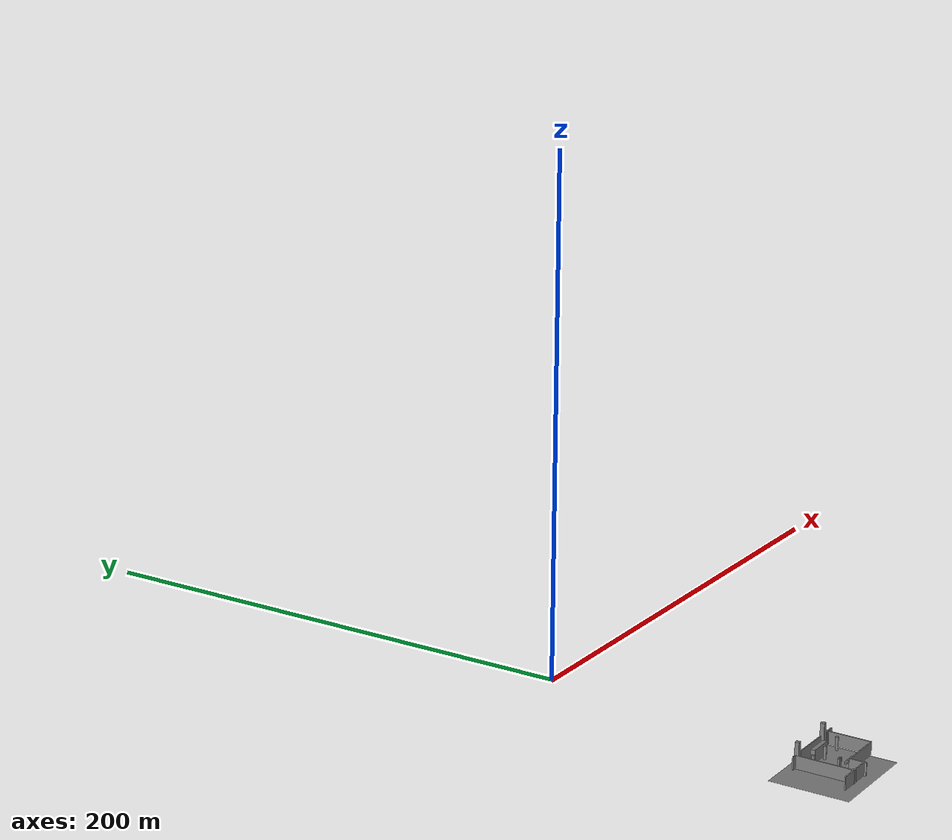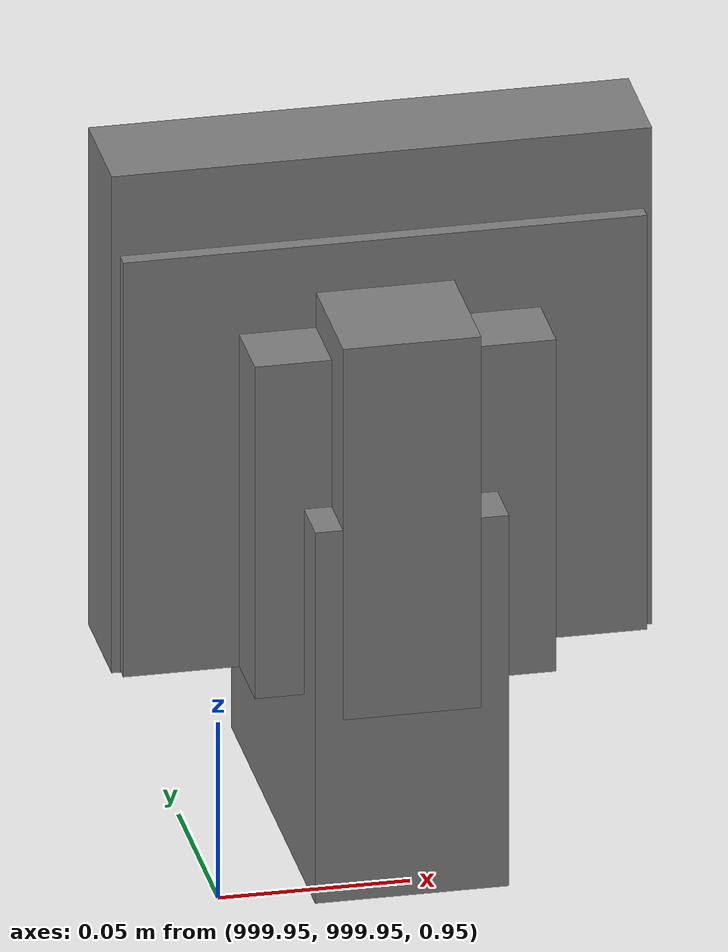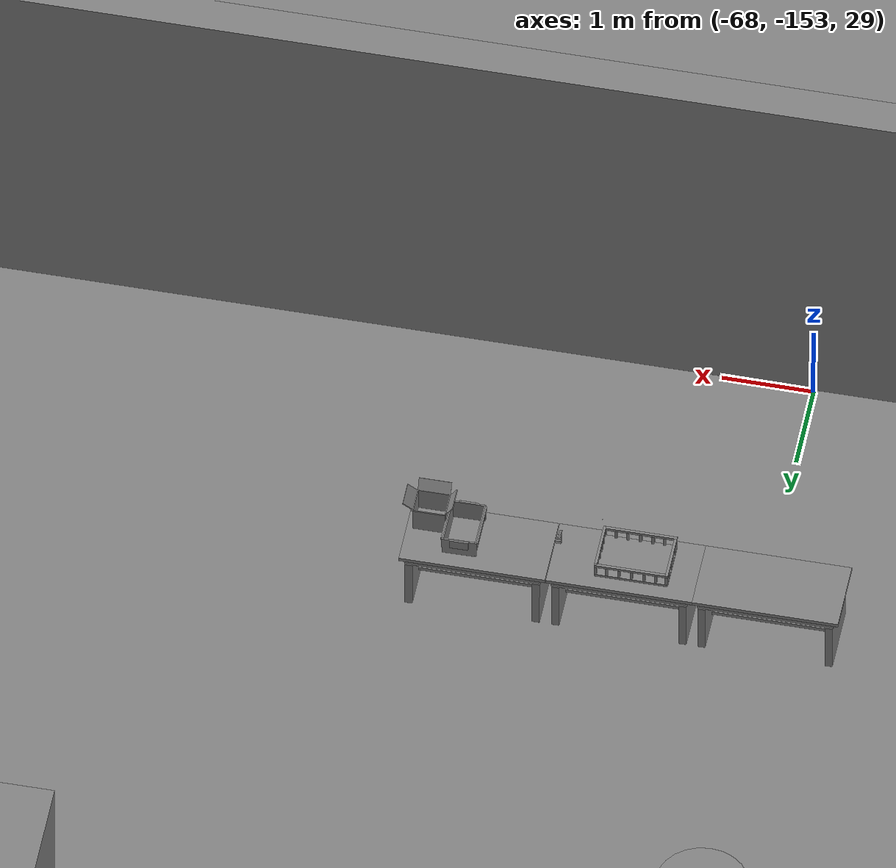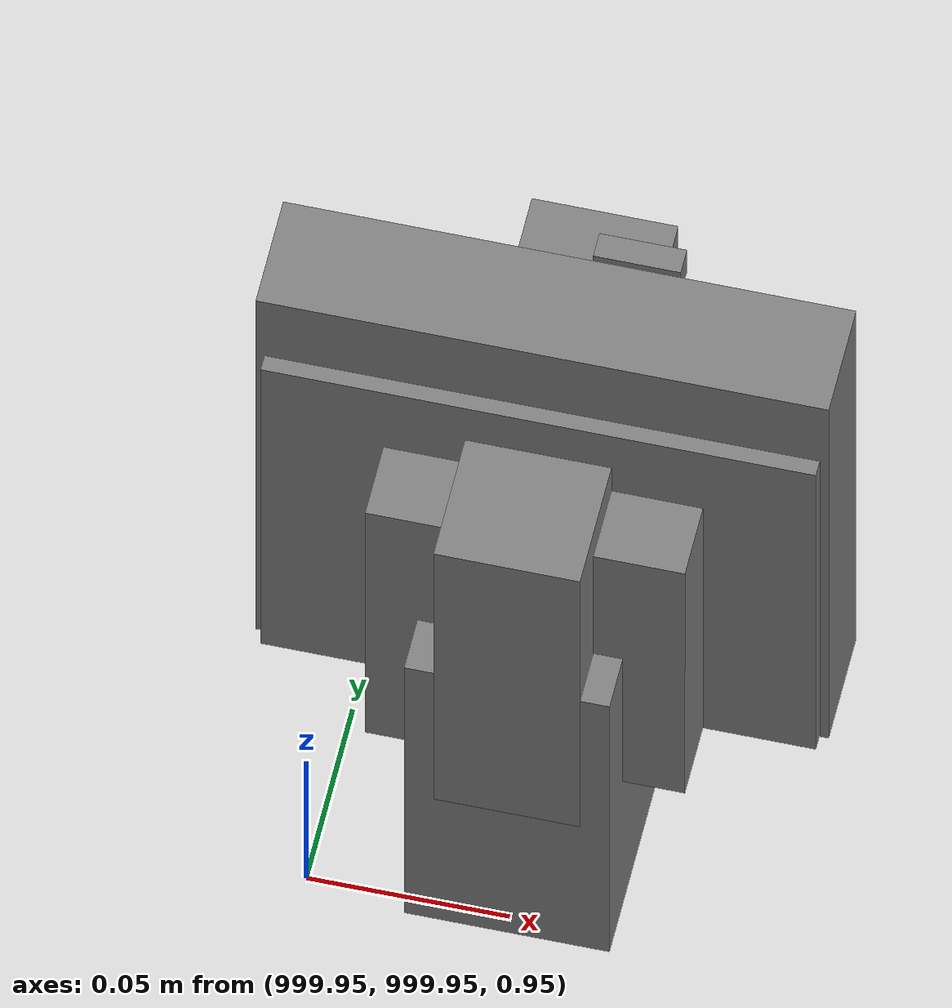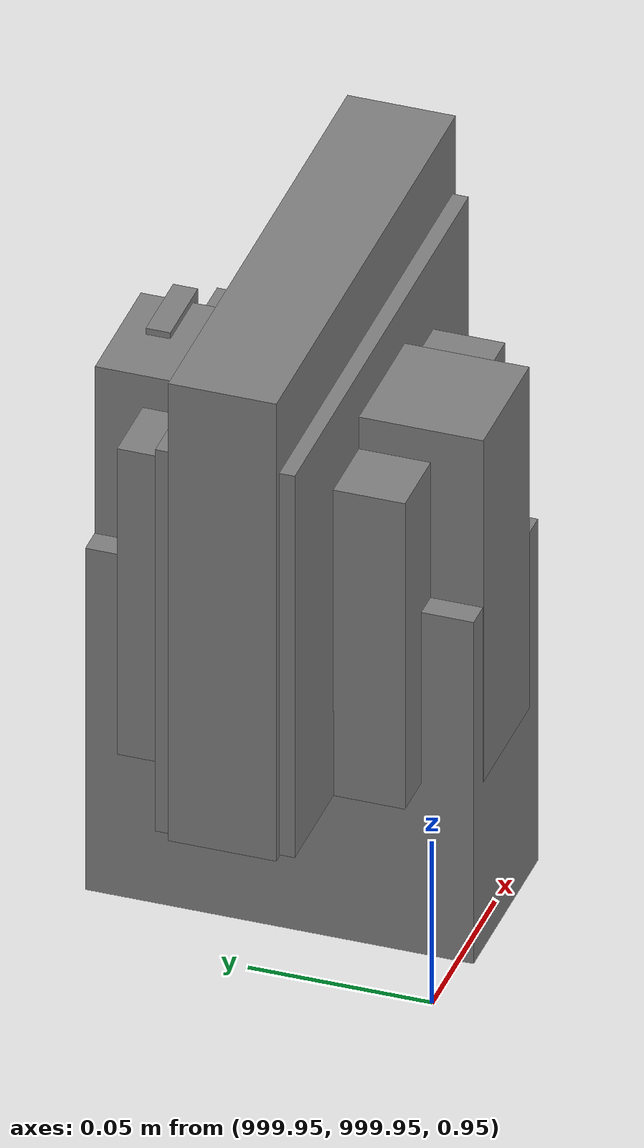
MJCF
<mujoco>
    <option gravity="0.000000000 0.000000000 -9.810000420" timestep="0.0049999999" integrator="implicitfast" density="1.225" viscosity="1.8000001e-05" noslip_iterations="10" iterations="100" sdf_iterations="50">
        <flag multiccd="disable"/>
    </option>
    <size memory="1000M"/>
    <compiler coordinate="local"/>
    <worldbody>
        <light cutoff="30" pos="0 1 1" dir="0 -1 -2"/>
        <light cutoff="30" pos="0 -1 1" dir="0 1 -2"/>
        <body pos="-64.866622925 -149.383972168 30.183746338" euler="89.999984741 89.999946594 0.000000000" name="openloong_gripper_2f85_fix_base_usda_bluebox_01">
            <geom contype="1" conaffinity="1" density="1000" type="box" material="" rgba="0.500000000 0.500000000 0.500000000 1.000000000" solimp="0.899999976 0.949999988 0.001000000" friction="1.000000000 0.005000000 0.000100000" solref="0.020000000 1.000000000" margin="0" condim="3" group="0" pos="0.276580811 0.187225342 0.000068665" quat="0.707106948 0.000077471 0.707106352 0.000077486" size="0.100000001 0.057999998 0.010000000" name="openloong_gripper_2f85_fix_base_usda_geom_DA650E7B_5C7C_490C_9280_C031693C87FE"/>
            <geom contype="1" conaffinity="1" density="1000" type="box" material="" rgba="0.500000000 0.500000000 0.500000000 1.000000000" solimp="0.899999976 0.949999988 0.001000000" friction="1.000000000 0.005000000 0.000100000" solref="0.020000000 1.000000000" margin="0" condim="3" group="0" pos="0.000000000 0.002883911 0.000000000" quat="0.999999881 0.000000000 0.000000000 0.000000000" size="0.254000008 0.003000000 0.172000006" name="openloong_gripper_2f85_fix_base_usda_geom_2704CAC9_FE5C_4AE4_BF16_CA7173BE18E1"/>
            <geom contype="1" conaffinity="1" density="1000" type="box" material="" rgba="0.500000000 0.500000000 0.500000000 1.000000000" solimp="0.899999976 0.949999988 0.001000000" friction="1.000000000 0.005000000 0.000100000" solref="0.020000000 1.000000000" margin="0" condim="3" group="0" pos="0.000000000 0.124874115 0.173484802" quat="0.999796331 0.020176515 -0.000000015 0.000000030" size="0.259999990 0.119999997 0.007000000" name="openloong_gripper_2f85_fix_base_usda_geom_2E256844_CA68_4F92_886E_2B4448971F6E"/>
            <geom contype="1" conaffinity="1" density="1000" type="box" material="" rgba="0.500000000 0.500000000 0.500000000 1.000000000" solimp="0.899999976 0.949999988 0.001000000" friction="1.000000000 0.005000000 0.000100000" solref="0.020000000 1.000000000" margin="0" condim="3" group="0" pos="0.000000000 0.124874115 -0.173469543" quat="0.999796331 -0.020176545 -0.000000015 0.000000000" size="0.259999990 0.119999997 0.007000000" name="openloong_gripper_2f85_fix_base_usda_geom_84AD24F1_2B83_49A5_B15E_B6EBDFE1AE22"/>
            <geom contype="1" conaffinity="1" density="1000" type="box" material="" rgba="0.500000000 0.500000000 0.500000000 1.000000000" solimp="0.899999976 0.949999988 0.001000000" friction="1.000000000 0.005000000 0.000100000" solref="0.020000000 1.000000000" margin="0" condim="3" group="0" pos="0.000000000 0.214008331 0.188980103" quat="0.999912977 0.013176724 0.000000015 0.000000000" size="0.259999990 0.029999999 0.012500000" name="openloong_gripper_2f85_fix_base_usda_geom_5F62B883_B545_4600_8826_45D4F36290C5"/>
            <geom contype="1" conaffinity="1" density="1000" type="box" material="" rgba="0.500000000 0.500000000 0.500000000 1.000000000" solimp="0.899999976 0.949999988 0.001000000" friction="1.000000000 0.005000000 0.000100000" solref="0.020000000 1.000000000" margin="0" condim="3" group="0" pos="-0.258361816 0.125289917 0.001876831" quat="0.702796936 -0.020792112 0.710783124 0.020769298" size="0.189999998 0.119999997 0.009000000" name="openloong_gripper_2f85_fix_base_usda_geom_40BBB2A5_1785_42BC_9E46_6D77E37DB728"/>
            <geom contype="1" conaffinity="1" density="1000" type="box" material="" rgba="0.500000000 0.500000000 0.500000000 1.000000000" solimp="0.899999976 0.949999988 0.001000000" friction="1.000000000 0.005000000 0.000100000" solref="0.020000000 1.000000000" margin="0" condim="3" group="0" pos="0.000000000 0.214008331 -0.188980103" quat="0.999912977 -0.013176769 0.000000030 0.000000015" size="0.259999990 0.029999999 0.012500000" name="openloong_gripper_2f85_fix_base_usda_geom_62CA2FF5_513E_4097_ADD6_B5D8502B676E"/>
            <geom contype="1" conaffinity="1" density="1000" type="box" material="" rgba="0.500000000 0.500000000 0.500000000 1.000000000" solimp="0.899999976 0.949999988 0.001000000" friction="1.000000000 0.005000000 0.000100000" solref="0.020000000 1.000000000" margin="0" condim="3" group="0" pos="-0.276611328 0.187225342 0.000068665" quat="0.707106650 0.000077441 0.707106709 0.000077456" size="0.100000001 0.057999998 0.010000000" name="openloong_gripper_2f85_fix_base_usda_geom_4C435147_45B5_499F_84E1_493227416A7B"/>
            <geom contype="1" conaffinity="1" density="1000" type="box" material="" rgba="0.500000000 0.500000000 0.500000000 1.000000000" solimp="0.899999976 0.949999988 0.001000000" friction="1.000000000 0.005000000 0.000100000" solref="0.020000000 1.000000000" margin="0" condim="3" group="0" pos="0.258331299 0.125289917 0.001876831" quat="0.702851415 0.018856421 0.710823774 -0.019329369" size="0.189999998 0.119999997 0.009000000" name="openloong_gripper_2f85_fix_base_usda_geom_B26B5D6F_5B16_4570_BED4_E1BB71A6B9D2"/>
            <freejoint name="openloong_gripper_2f85_fix_base_usda_bluebox_01_joint"/>
            <site size="0.005000000 0.005000000 0.005000000" rgba="0.500000000 0.500000000 0.500000000 1.000000000" pos="0.000000000 0.000000000 0.000000000" quat="0.999961913 0.008726534 0.000000000 0.000000000" group="0" type="sphere" name="openloong_gripper_2f85_fix_base_usda_bluebox_01site"/>
        </body>
        <body pos="-64.496299744 -149.491867065 30.235729218" euler="0.000000000 0.000000000 89.999946594" name="openloong_gripper_2f85_fix_base_usda_cardboardbox_01">
            <geom contype="1" conaffinity="1" density="1000" type="box" material="" rgba="0.500000000 0.500000000 0.500000000 1.000000000" solimp="0.899999976 0.949999988 0.001000000" friction="1.000000000 0.005000000 0.000100000" solref="0.020000000 1.000000000" margin="0" condim="3" group="0" pos="-0.003166199 -0.004086494 0.005052090" quat="1.000000000 0.000000000 0.000000000 0.000000000" size="0.142499998 0.177500010 0.005000000" name="openloong_gripper_2f85_fix_base_usda_geom_37BD033E_2C26_48D6_98E6_080FEAD7EF58"/>
            <geom contype="1" conaffinity="1" density="1000" type="box" material="" rgba="0.500000000 0.500000000 0.500000000 1.000000000" solimp="0.899999976 0.949999988 0.001000000" friction="1.000000000 0.005000000 0.000100000" solref="0.020000000 1.000000000" margin="0" condim="3" group="0" pos="-0.003166199 0.170316696 0.150570869" quat="1.000000000 0.000000000 0.000000000 0.000000000" size="0.142499998 0.005000000 0.149999991" name="openloong_gripper_2f85_fix_base_usda_geom_FF5953BA_1CD2_48BE_AFDA_A166F29D5993"/>
            <geom contype="1" conaffinity="1" density="1000" type="box" material="" rgba="0.500000000 0.500000000 0.500000000 1.000000000" solimp="0.899999976 0.949999988 0.001000000" friction="1.000000000 0.005000000 0.000100000" solref="0.020000000 1.000000000" margin="0" condim="3" group="0" pos="-0.147399902 -0.005307198 0.150570869" quat="1.000000000 0.000000000 0.000000000 0.000000000" size="0.005000000 0.177500010 0.149999991" name="openloong_gripper_2f85_fix_base_usda_geom_B9424864_5EAC_4915_832E_E3012B425FD8"/>
            <geom contype="1" conaffinity="1" density="1000" type="box" material="" rgba="0.500000000 0.500000000 0.500000000 1.000000000" solimp="0.899999976 0.949999988 0.001000000" friction="1.000000000 0.005000000 0.000100000" solref="0.020000000 1.000000000" margin="0" condim="3" group="0" pos="0.140275955 -0.005307198 0.150570869" quat="1.000000000 0.000000000 0.000000000 0.000000000" size="0.005000000 0.177500010 0.149999991" name="openloong_gripper_2f85_fix_base_usda_geom_BF7F779B_5A4F_4AF2_ABA8_6FC16AC3CC5C"/>
            <geom contype="1" conaffinity="1" density="1000" type="box" material="" rgba="0.500000000 0.500000000 0.500000000 1.000000000" solimp="0.899999976 0.949999988 0.001000000" friction="1.000000000 0.005000000 0.000100000" solref="0.020000000 1.000000000" margin="0" condim="3" group="0" pos="-0.003166199 -0.181550980 0.150570869" quat="1.000000000 0.000000000 0.000000000 0.000000000" size="0.142499998 0.005000000 0.149999991" name="openloong_gripper_2f85_fix_base_usda_geom_387591D1_1E60_4728_A7DF_0C3BC943C396"/>
            <freejoint name="openloong_gripper_2f85_fix_base_usda_cardboardbox_01_joint"/>
            <site size="0.005000000 0.005000000 0.005000000" rgba="0.500000000 0.500000000 0.500000000 1.000000000" pos="0.000000000 0.000000000 0.000000000" quat="0.999961913 0.008726535 0.000000000 0.000000000" group="0" type="sphere" name="openloong_gripper_2f85_fix_base_usda_site_A06D3E55_87E8_46D8_97BE_6F867C76DE0E"/>
            <body pos="0.139160156 -0.004048347 0.301930904" euler="-179.999954224 49.383502960 179.999954224" name="openloong_gripper_2f85_fix_base_usda_A1_006">
                <geom contype="1" conaffinity="1" density="1000" type="box" material="" rgba="0.500000000 0.500000000 0.500000000 1.000000000" solimp="0.899999976 0.949999988 0.001000000" friction="1.000000000 0.005000000 0.000100000" solref="0.020000000 1.000000000" margin="0" condim="3" group="0" pos="-0.071587563 0.000009537 0.001745224" quat="0.999999881 0.000000000 0.000000000 0.000000000" size="0.071249999 0.179999992 0.002500000" name="openloong_gripper_2f85_fix_base_usda_geom_43B1663D_B3B1_419F_AE62_742E65BBF3BD"/>
                <joint armature="0" stiffness="0.07" damping="0.0099999998" axis="0.000000 1.000000 0.000000" type="hinge" name="openloong_gripper_2f85_fix_base_usda_A1_006"/>
            </body>
            <body pos="-0.145902634 -0.004086494 0.301938057" euler="-180.000000000 -60.000011444 -180.000000000" name="openloong_gripper_2f85_fix_base_usda_A2_006">
                <geom contype="1" conaffinity="1" density="1000" type="box" material="" rgba="0.500000000 0.500000000 0.500000000 1.000000000" solimp="0.899999976 0.949999988 0.001000000" friction="1.000000000 0.005000000 0.000100000" solref="0.020000000 1.000000000" margin="0" condim="3" group="0" pos="0.071268082 0.000009537 0.002717972" quat="0.000002921 0.000000000 -0.000000030 0.999999881" size="0.071249999 0.179999992 0.002500000" name="openloong_gripper_2f85_fix_base_usda_geom_17927D5E_583D_42D4_8D6A_F71DAD5B0308"/>
                <joint armature="0" stiffness="0.07" damping="0.0099999998" axis="0.000000 1.000000 0.000000" type="hinge" name="openloong_gripper_2f85_fix_base_usda_A2_006"/>
            </body>
            <body pos="-0.003385544 0.175991058 0.301930904" euler="-125.858116150 -0.000004561 0.000002331" name="openloong_gripper_2f85_fix_base_usda_B2_006">
                <geom contype="1" conaffinity="1" density="1000" type="box" material="" rgba="0.500000000 0.500000000 0.500000000 1.000000000" solimp="0.899999976 0.949999988 0.001000000" friction="1.000000000 0.005000000 0.000100000" solref="0.020000000 1.000000000" margin="0" condim="3" group="0" pos="0.000009537 -0.070939064 -0.002470016" quat="0.999614120 0.027776197 -0.000000015 0.000000030" size="0.137500003 0.064999998 0.005000000" name="openloong_gripper_2f85_fix_base_usda_geom_B9D6EA9A_543C_4A6C_9428_2EDFB87E1F32"/>
                <joint armature="0" stiffness="0.07" damping="0.0099999998" axis="1.000000 0.000000 0.000000" type="hinge" name="openloong_gripper_2f85_fix_base_usda_B2_006"/>
            </body>
            <body pos="-0.003385544 -0.184140205 0.301938057" euler="147.805557251 0.000000000 0.000000000" name="openloong_gripper_2f85_fix_base_usda_B1_006">
                <geom contype="1" conaffinity="1" density="1000" type="box" material="" rgba="0.500000000 0.500000000 0.500000000 1.000000000" solimp="0.899999976 0.949999988 0.001000000" friction="1.000000000 0.005000000 0.000100000" solref="0.020000000 1.000000000" margin="0" condim="3" group="0" pos="-0.000028610 0.070202351 -0.002703667" quat="0.999614179 -0.027776167 0.000000000 0.000000000" size="0.137500003 0.064999998 0.005000000" name="openloong_gripper_2f85_fix_base_usda_geom_044484BE_7464_4697_9DE9_9A8E52B9B0CB"/>
                <joint armature="0" stiffness="0.07" damping="0.0099999998" axis="1.000000 0.000000 0.000000" type="hinge" name="openloong_gripper_2f85_fix_base_usda_B1_006"/>
            </body>
        </body>
        <body pos="-65.882858276 -149.481979370 30.229999542" euler="-64.487716675 0.000000000 0.000000000" name="openloong_gripper_2f85_fix_base_usda_Barcode">
            <geom contype="1" conaffinity="1" density="1000" type="box" material="" rgba="0.500000000 0.500000000 0.500000000 1.000000000" solimp="0.899999976 0.949999988 0.001000000" friction="1.000000000 0.005000000 0.000100000" solref="0.020000000 1.000000000" margin="0" condim="3" group="0" pos="0.000000000 0.013038635 0.001419067" quat="0.000000000 0.000000000 0.000000000 1.000000119" size="0.034000002 0.010000000 0.017999999" name="openloong_gripper_2f85_fix_base_usda_geom_811ABFCA_4106_42A8_848A_2235B99D5B7F"/>
            <geom contype="1" conaffinity="1" density="1000" type="box" material="" rgba="0.500000000 0.500000000 0.500000000 1.000000000" solimp="0.899999976 0.949999988 0.001000000" friction="1.000000000 0.005000000 0.000100000" solref="0.020000000 1.000000000" margin="0" condim="3" group="0" pos="0.000000000 -0.035301208 -0.007095337" quat="0.000000000 0.000000000 -0.043619365 0.999048233" size="0.028999999 0.010000000 0.020000000" name="openloong_gripper_2f85_fix_base_usda_geom_077C5ABB_CE4D_4564_8F89_AC02DE9DA813"/>
            <geom contype="1" conaffinity="1" density="1000" type="box" material="" rgba="0.500000000 0.500000000 0.500000000 1.000000000" solimp="0.899999976 0.949999988 0.001000000" friction="1.000000000 0.005000000 0.000100000" solref="0.020000000 1.000000000" margin="0" condim="3" group="0" pos="0.000000000 -0.043411255 -0.011749268" quat="0.922262907 0.386563420 0.000000000 0.000000000" size="0.026000001 0.010000000 0.020000000" name="openloong_gripper_2f85_fix_base_usda_geom_5AB6201B_CF18_49AF_9F7B_E1E7D2BF568C"/>
            <geom contype="1" conaffinity="1" density="1000" type="box" material="" rgba="0.500000000 0.500000000 0.500000000 1.000000000" solimp="0.899999976 0.949999988 0.001000000" friction="1.000000000 0.005000000 0.000100000" solref="0.020000000 1.000000000" margin="0" condim="3" group="0" pos="0.000000000 -0.016967773 -0.031860352" quat="0.000000000 0.000000000 0.000000000 1.000000119" size="0.008000000 0.010000000 0.013000000" name="openloong_gripper_2f85_fix_base_usda_geom_AC30F0B3_5D33_4D49_8532_73DD1AC30494"/>
            <geom contype="1" conaffinity="1" density="1000" type="box" material="" rgba="0.500000000 0.500000000 0.500000000 1.000000000" solimp="0.899999976 0.949999988 0.001000000" friction="1.000000000 0.005000000 0.000100000" solref="0.020000000 1.000000000" margin="0" condim="3" group="0" pos="0.000000000 -0.001869202 0.000312805" quat="0.953716993 0.300705761 0.000000000 0.000000000" size="0.032000002 0.010000000 0.018999999" name="openloong_gripper_2f85_fix_base_usda_geom_B7186A31_6D08_4900_AB66_950876B827A9"/>
            <geom contype="1" conaffinity="1" density="1000" type="box" material="" rgba="0.500000000 0.500000000 0.500000000 1.000000000" solimp="0.899999976 0.949999988 0.001000000" friction="1.000000000 0.005000000 0.000100000" solref="0.020000000 1.000000000" margin="0" condim="3" group="0" pos="0.000000000 -0.019531250 -0.003173828" quat="0.953716993 0.300705761 0.000000000 0.000000000" size="0.030999999 0.010000000 0.020000000" name="openloong_gripper_2f85_fix_base_usda_geom_18507082_2319_4903_9B6F_4D436249E148"/>
            <geom contype="1" conaffinity="1" density="1000" type="box" material="" rgba="0.500000000 0.500000000 0.500000000 1.000000000" solimp="0.899999976 0.949999988 0.001000000" friction="1.000000000 0.005000000 0.000100000" solref="0.020000000 1.000000000" margin="0" condim="3" group="0" pos="0.000000000 -0.035301208 -0.007095337" quat="0.953716993 0.300705761 0.000000000 0.000000000" size="0.028999999 0.010000000 0.020000000" name="openloong_gripper_2f85_fix_base_usda_geom_D0869370_105E_45F4_A950_F8047FAB59C1"/>
            <geom contype="1" conaffinity="1" density="1000" type="box" material="" rgba="0.500000000 0.500000000 0.500000000 1.000000000" solimp="0.899999976 0.949999988 0.001000000" friction="1.000000000 0.005000000 0.000100000" solref="0.020000000 1.000000000" margin="0" condim="3" group="0" pos="0.000000000 -0.042617798 -0.071121216" quat="0.000000000 0.000000000 0.000000000 1.000000119" size="0.013000000 0.021000000 0.059999999" name="openloong_gripper_2f85_fix_base_usda_geom_70AF5941_3E17_4516_9A40_1ACFBE9D981E"/>
            <freejoint name="openloong_gripper_2f85_fix_base_usda_Barcode_joint"/>
            <site size="0.005000000 0.005000000 0.005000000" rgba="0.500000000 0.500000000 0.500000000 1.000000000" pos="0.000000000 0.000000000 0.000000000" quat="1.000000000 0.000000000 0.000000000 0.000000000" group="0" type="sphere" name="openloong_gripper_2f85_fix_base_usda_Barcode_site"/>
        </body>
        <body pos="-66.745018005 -149.392349243 30.184000015" euler="0.000000000 0.000000000 89.999946594" name="[22332216167375]_Basket_01">
            <geom contype="1" conaffinity="1" density="1000" type="box" material="" rgba="0.500000000 0.500000000 0.500000000 1.000000000" solimp="0.899999976 0.949999988 0.001000000" friction="1.000000000 0.005000000 0.000100000" solref="0.020000000 1.000000000" margin="0" condim="3" group="0" pos="-0.052425385 0.389207840 0.089787483" quat="0.707107008 0.000000000 0.000000000 0.707106411" size="0.014249999 0.014249999 0.059999999" name="[22332216167375]_geom_EDD7CD8D_3E71_41A1_B805_244343F986D6"/>
            <geom contype="1" conaffinity="1" density="1000" type="box" material="" rgba="0.500000000 0.500000000 0.500000000 1.000000000" solimp="0.899999976 0.949999988 0.001000000" friction="1.000000000 0.005000000 0.000100000" solref="0.020000000 1.000000000" margin="0" condim="3" group="0" pos="0.264015198 -0.133043289 0.089787483" quat="0.707107008 0.000000000 0.000000000 0.707106411" size="0.014249999 0.014249999 0.059999999" name="[22332216167375]_geom_588AE513_CA7C_4563_BB67_B522B75CA3BE"/>
            <geom contype="1" conaffinity="1" density="1000" type="box" material="" rgba="0.500000000 0.500000000 0.500000000 1.000000000" solimp="0.899999976 0.949999988 0.001000000" friction="1.000000000 0.005000000 0.000100000" solref="0.020000000 1.000000000" margin="0" condim="3" group="0" pos="-0.264015198 -0.265548706 0.089793205" quat="0.707107008 0.000000000 0.000000000 0.707106411" size="0.014249999 0.014249999 0.059999999" name="[22332216167375]_geom_0CAD5ACD_F704_45B0_B116_905CA8CDB28A"/>
            <geom contype="1" conaffinity="1" density="1000" type="box" material="" rgba="0.500000000 0.500000000 0.500000000 1.000000000" solimp="0.899999976 0.949999988 0.001000000" friction="1.000000000 0.005000000 0.000100000" solref="0.020000000 1.000000000" margin="0" condim="3" group="0" pos="-0.160263062 -0.389322281 0.089793205" quat="0.707107008 0.000000000 0.000000000 0.707106411" size="0.014249999 0.014249999 0.059999999" name="[22332216167375]_geom_91843BDC_0CA1_4AE0_81A7_9FA58E341F1E"/>
            <geom contype="1" conaffinity="1" density="1000" type="box" material="" rgba="0.500000000 0.500000000 0.500000000 1.000000000" solimp="0.899999976 0.949999988 0.001000000" friction="1.000000000 0.005000000 0.000100000" solref="0.020000000 1.000000000" margin="0" condim="3" group="0" pos="0.162265778 -0.389322281 0.089787483" quat="0.707107008 0.000000000 0.000000000 0.707106411" size="0.014249999 0.014249999 0.059999999" name="[22332216167375]_geom_C430F5FF_F870_4E87_9B6A_97CE3469CF7D"/>
            <geom contype="1" conaffinity="1" density="1000" type="box" material="" rgba="0.500000000 0.500000000 0.500000000 1.000000000" solimp="0.899999976 0.949999988 0.001000000" friction="1.000000000 0.005000000 0.000100000" solref="0.020000000 1.000000000" margin="0" condim="3" group="0" pos="0.264015198 0.389207840 0.089787483" quat="0.707107008 0.000000000 0.000000000 0.707106411" size="0.014249999 0.014249999 0.059999999" name="[22332216167375]_geom_9FEA822C_B45C_45FF_B126_A941BF2BA29D"/>
            <geom contype="1" conaffinity="1" density="1000" type="box" material="" rgba="0.500000000 0.500000000 0.500000000 1.000000000" solimp="0.899999976 0.949999988 0.001000000" friction="1.000000000 0.005000000 0.000100000" solref="0.020000000 1.000000000" margin="0" condim="3" group="0" pos="-0.264015198 -0.133043289 0.089793205" quat="0.707107008 0.000000000 0.000000000 0.707106411" size="0.014249999 0.014249999 0.059999999" name="[22332216167375]_geom_EE77191F_E1CF_494D_A251_9159800C60C9"/>
            <geom contype="1" conaffinity="1" density="1000" type="box" material="" rgba="0.500000000 0.500000000 0.500000000 1.000000000" solimp="0.899999976 0.949999988 0.001000000" friction="1.000000000 0.005000000 0.000100000" solref="0.020000000 1.000000000" margin="0" condim="3" group="0" pos="-0.264026642 0.269256592 0.089793205" quat="0.707107008 0.000000000 0.000000000 0.707106411" size="0.014249999 0.014249999 0.059999999" name="[22332216167375]_geom_658AC601_D96D_488C_B4AA_F4E045BD25FC"/>
            <geom contype="1" conaffinity="1" density="1000" type="box" material="" rgba="0.500000000 0.500000000 0.500000000 1.000000000" solimp="0.899999976 0.949999988 0.001000000" friction="1.000000000 0.005000000 0.000100000" solref="0.020000000 1.000000000" margin="0" condim="3" group="0" pos="0.054462433 0.389207840 0.089787483" quat="0.707107008 0.000000000 0.000000000 0.707106411" size="0.014249999 0.014249999 0.059999999" name="[22332216167375]_geom_04CF787D_DE2F_4F8B_87BE_1CA670E265BB"/>
            <geom contype="1" conaffinity="1" density="1000" type="box" material="" rgba="0.500000000 0.500000000 0.500000000 1.000000000" solimp="0.899999976 0.949999988 0.001000000" friction="1.000000000 0.005000000 0.000100000" solref="0.020000000 1.000000000" margin="0" condim="3" group="0" pos="0.054462433 -0.389322281 0.089787483" quat="0.707107008 0.000000000 0.000000000 0.707106411" size="0.014249999 0.014249999 0.059999999" name="[22332216167375]_geom_4F3B4353_B4F1_4CBA_8364_F5551C5FFF4A"/>
            <geom contype="1" conaffinity="1" density="1000" type="box" material="" rgba="0.500000000 0.500000000 0.500000000 1.000000000" solimp="0.899999976 0.949999988 0.001000000" friction="1.000000000 0.005000000 0.000100000" solref="0.020000000 1.000000000" margin="0" condim="3" group="0" pos="0.264015198 0.269256592 0.089793205" quat="0.707107008 0.000000000 0.000000000 0.707106411" size="0.014249999 0.014249999 0.059999999" name="[22332216167375]_geom_7E303E53_3EF3_4F52_BC43_D41957E1D3F9"/>
            <geom contype="1" conaffinity="1" density="1000" type="box" material="" rgba="0.500000000 0.500000000 0.500000000 1.000000000" solimp="0.899999976 0.949999988 0.001000000" friction="1.000000000 0.005000000 0.000100000" solref="0.020000000 1.000000000" margin="0" condim="3" group="0" pos="0.264015198 -0.389322281 0.089787483" quat="0.707107008 0.000000000 0.000000000 0.707106411" size="0.014249999 0.014249999 0.059999999" name="[22332216167375]_geom_9F0AF5AE_F764_4E2B_9B17_E6F945AADCFD"/>
            <geom contype="1" conaffinity="1" density="1000" type="box" material="" rgba="0.500000000 0.500000000 0.500000000 1.000000000" solimp="0.899999976 0.949999988 0.001000000" friction="1.000000000 0.005000000 0.000100000" solref="0.020000000 1.000000000" margin="0" condim="3" group="0" pos="0.000000000 0.000000000 0.015998840" quat="0.707107008 0.000000000 0.000000000 0.707106411" size="0.403499991 0.279000014 0.015750000" name="[22332216167375]_geom_99D74072_983A_4630_9029_3D4B2A922865"/>
            <geom contype="1" conaffinity="1" density="1000" type="box" material="" rgba="0.500000000 0.500000000 0.500000000 1.000000000" solimp="0.899999976 0.949999988 0.001000000" friction="1.000000000 0.005000000 0.000100000" solref="0.020000000 1.000000000" margin="0" condim="3" group="0" pos="0.000000000 -0.389476776 0.163619041" quat="0.707107008 0.000000000 0.000000000 0.707106411" size="0.015000000 0.277500004 0.015750000" name="[22332216167375]_geom_968D2CDF_1DAD_4466_9472_B1F8F4736550"/>
            <geom contype="1" conaffinity="1" density="1000" type="box" material="" rgba="0.500000000 0.500000000 0.500000000 1.000000000" solimp="0.899999976 0.949999988 0.001000000" friction="1.000000000 0.005000000 0.000100000" solref="0.020000000 1.000000000" margin="0" condim="3" group="0" pos="0.162265778 0.389207840 0.089787483" quat="0.707107008 0.000000000 0.000000000 0.707106411" size="0.014249999 0.014249999 0.059999999" name="[22332216167375]_geom_4546060A_4A20_439C_A46C_6195E4D98E6B"/>
            <geom contype="1" conaffinity="1" density="1000" type="box" material="" rgba="0.500000000 0.500000000 0.500000000 1.000000000" solimp="0.899999976 0.949999988 0.001000000" friction="1.000000000 0.005000000 0.000100000" solref="0.020000000 1.000000000" margin="0" condim="3" group="0" pos="0.000000000 0.389471054 0.163619041" quat="0.707107008 0.000000000 0.000000000 0.707106411" size="0.015000000 0.277500004 0.015750000" name="[22332216167375]_geom_267DEE91_80B3_4189_8C23_B8973CCA5CE2"/>
            <geom contype="1" conaffinity="1" density="1000" type="box" material="" rgba="0.500000000 0.500000000 0.500000000 1.000000000" solimp="0.899999976 0.949999988 0.001000000" friction="1.000000000 0.005000000 0.000100000" solref="0.020000000 1.000000000" margin="0" condim="3" group="0" pos="-0.263511658 0.000000000 0.163619041" quat="0.707107008 0.000000000 0.000000000 0.707106411" size="0.403499991 0.015000000 0.015750000" name="[22332216167375]_geom_D392427D_2DCD_461A_9A16_75A182B45BD8"/>
            <geom contype="1" conaffinity="1" density="1000" type="box" material="" rgba="0.500000000 0.500000000 0.500000000 1.000000000" solimp="0.899999976 0.949999988 0.001000000" friction="1.000000000 0.005000000 0.000100000" solref="0.020000000 1.000000000" margin="0" condim="3" group="0" pos="-0.264015198 0.141334534 0.089793205" quat="0.707107008 0.000000000 0.000000000 0.707106411" size="0.014249999 0.014249999 0.059999999" name="[22332216167375]_geom_E25763D5_6DCA_46F6_A9EB_36BE2FF03CE3"/>
            <geom contype="1" conaffinity="1" density="1000" type="box" material="" rgba="0.500000000 0.500000000 0.500000000 1.000000000" solimp="0.899999976 0.949999988 0.001000000" friction="1.000000000 0.005000000 0.000100000" solref="0.020000000 1.000000000" margin="0" condim="3" group="0" pos="0.264015198 -0.265548706 0.089787483" quat="0.707107008 0.000000000 0.000000000 0.707106411" size="0.014249999 0.014249999 0.059999999" name="[22332216167375]_geom_427C1B8D_F5AF_4EC7_B6D4_6CA6AB0D5E5C"/>
            <geom contype="1" conaffinity="1" density="1000" type="box" material="" rgba="0.500000000 0.500000000 0.500000000 1.000000000" solimp="0.899999976 0.949999988 0.001000000" friction="1.000000000 0.005000000 0.000100000" solref="0.020000000 1.000000000" margin="0" condim="3" group="0" pos="-0.160263062 0.389207840 0.089787483" quat="0.707107008 0.000000000 0.000000000 0.707106411" size="0.014249999 0.014249999 0.059999999" name="[22332216167375]_geom_97613944_1A33_40A0_A513_ADB5E941AD47"/>
            <geom contype="1" conaffinity="1" density="1000" type="box" material="" rgba="0.500000000 0.500000000 0.500000000 1.000000000" solimp="0.899999976 0.949999988 0.001000000" friction="1.000000000 0.005000000 0.000100000" solref="0.020000000 1.000000000" margin="0" condim="3" group="0" pos="-0.052425385 -0.389322281 0.089787483" quat="0.707107008 0.000000000 0.000000000 0.707106411" size="0.014249999 0.014249999 0.059999999" name="[22332216167375]_geom_8A357646_29E6_44C7_B895_0821C147D1E5"/>
            <geom contype="1" conaffinity="1" density="1000" type="box" material="" rgba="0.500000000 0.500000000 0.500000000 1.000000000" solimp="0.899999976 0.949999988 0.001000000" friction="1.000000000 0.005000000 0.000100000" solref="0.020000000 1.000000000" margin="0" condim="3" group="0" pos="-0.264026642 -0.389322281 0.089793205" quat="0.707107008 0.000000000 0.000000000 0.707106411" size="0.014249999 0.014249999 0.059999999" name="[22332216167375]_geom_87AB42A7_8C50_4E2E_B688_6DD5A19CF28D"/>
            <geom contype="1" conaffinity="1" density="1000" type="box" material="" rgba="0.500000000 0.500000000 0.500000000 1.000000000" solimp="0.899999976 0.949999988 0.001000000" friction="1.000000000 0.005000000 0.000100000" solref="0.020000000 1.000000000" margin="0" condim="3" group="0" pos="0.264015198 0.141334534 0.089787483" quat="0.707107008 0.000000000 0.000000000 0.707106411" size="0.014249999 0.014249999 0.059999999" name="[22332216167375]_geom_402F8DAD_7E11_4B65_A7DD_E9F3767F0025"/>
            <geom contype="1" conaffinity="1" density="1000" type="box" material="" rgba="0.500000000 0.500000000 0.500000000 1.000000000" solimp="0.899999976 0.949999988 0.001000000" friction="1.000000000 0.005000000 0.000100000" solref="0.020000000 1.000000000" margin="0" condim="3" group="0" pos="-0.264015198 0.389207840 0.089793205" quat="0.707107008 0.000000000 0.000000000 0.707106411" size="0.014249999 0.014249999 0.059999999" name="[22332216167375]_geom_4796EE0A_DAAB_422A_BF56_CE32E923392F"/>
            <geom contype="1" conaffinity="1" density="1000" type="box" material="" rgba="0.500000000 0.500000000 0.500000000 1.000000000" solimp="0.899999976 0.949999988 0.001000000" friction="1.000000000 0.005000000 0.000100000" solref="0.020000000 1.000000000" margin="0" condim="3" group="0" pos="0.264015198 0.004480362 0.089787483" quat="0.707107008 0.000000000 0.000000000 0.707106411" size="0.014249999 0.014249999 0.059999999" name="[22332216167375]_geom_EDAC981D_1E76_45F1_A156_C87B6D1B0482"/>
            <geom contype="1" conaffinity="1" density="1000" type="box" material="" rgba="0.500000000 0.500000000 0.500000000 1.000000000" solimp="0.899999976 0.949999988 0.001000000" friction="1.000000000 0.005000000 0.000100000" solref="0.020000000 1.000000000" margin="0" condim="3" group="0" pos="0.263694763 -0.000011444 0.163619041" quat="0.707107008 0.000000000 0.000000000 0.707106411" size="0.403499991 0.015000000 0.015750000" name="[22332216167375]_geom_FEF4CC54_46A0_44E3_BEE9_72181BE8AF1C"/>
            <geom contype="1" conaffinity="1" density="1000" type="box" material="" rgba="0.500000000 0.500000000 0.500000000 1.000000000" solimp="0.899999976 0.949999988 0.001000000" friction="1.000000000 0.005000000 0.000100000" solref="0.020000000 1.000000000" margin="0" condim="3" group="0" pos="-0.264015198 0.004480362 0.089793205" quat="0.707107008 0.000000000 0.000000000 0.707106411" size="0.014249999 0.014249999 0.059999999" name="[22332216167375]_geom_F3DD8997_A8B2_4775_B498_6CBF4BEEED99"/>
            <freejoint name="[22332216167375]_joint_FFB1A5E8_720B_4055_9519_601F5676B03B"/>
        </body>
        <body pos="0.000000000 0.000000000 0.000000000" euler="0.000000000 0.000000000 0.000000000" name="Static Objects_Static Objects">
            <geom contype="1" conaffinity="1" density="1000" type="box" material="" rgba="0.500000000 0.500000000 0.500000000 1.000000000" solimp="0.899999976 0.949999988 0.001000000" friction="1.000000000 0.005000000 0.000100000" solref="0.020000000 1.000000000" margin="0" condim="3" group="0" pos="-67.544113159 -149.365814209 29.727830887" quat="0.500000417 0.499999970 0.499999553 0.499999970" size="0.381000012 0.319999993 0.041000001" name="Static Objects_geom_5E884A60_4977_432E_BA0C_A64A175B4F1F"/>
            <geom contype="1" conaffinity="1" density="1000" type="box" material="" rgba="0.500000000 0.500000000 0.500000000 1.000000000" solimp="0.899999976 0.949999988 0.001000000" friction="1.000000000 0.005000000 0.000100000" solref="0.020000000 1.000000000" margin="0" condim="3" group="0" pos="-68.239501953 -149.365814209 30.086868286" quat="0.500000417 0.499999970 0.499999553 0.499999970" size="0.370999992 0.039500002 0.745000005" name="Static Objects_geom_C016048D_3DB9_484B_832F_CC3211016DF9"/>
            <geom contype="1" conaffinity="1" density="1000" type="box" material="" rgba="0.500000000 0.500000000 0.500000000 1.000000000" solimp="0.899999976 0.949999988 0.001000000" friction="1.000000000 0.005000000 0.000100000" solref="0.020000000 1.000000000" margin="0" condim="3" group="0" pos="-68.239501953 -149.365814209 30.147235870" quat="0.500000417 0.499999970 0.499999553 0.499999970" size="0.400000006 0.022000000 0.800000012" name="Static Objects_geom_58C09B4B_8993_4FD0_83BD_B8060B5CD262"/>
            <geom contype="1" conaffinity="1" density="1000" type="box" material="" rgba="0.500000000 0.500000000 0.500000000 1.000000000" solimp="0.899999976 0.949999988 0.001000000" friction="1.000000000 0.005000000 0.000100000" solref="0.020000000 1.000000000" margin="0" condim="3" group="0" pos="-68.934890747 -149.365814209 29.727830887" quat="0.500000417 0.499999970 0.499999553 0.499999970" size="0.381000012 0.319999993 0.041000001" name="Static Objects_geom_C00EE1B9_82D5_430E_9D38_5F9DF092A49C"/>
            <geom contype="1" conaffinity="1" density="1000" type="box" material="" rgba="0.500000000 0.500000000 0.500000000 1.000000000" solimp="0.899999976 0.949999988 0.001000000" friction="1.000000000 0.005000000 0.000100000" solref="0.020000000 1.000000000" margin="0" condim="3" group="0" pos="-68.239501953 -149.365814209 29.561563492" quat="0.500000417 0.499999970 0.499999553 0.499999970" size="0.020000000 0.022000000 0.660000026" name="Static Objects_geom_C4E11625_6209_476E_9057_76260EE2F206"/>
            <geom contype="1" conaffinity="1" density="1000" type="box" material="" rgba="0.500000000 0.500000000 0.500000000 1.000000000" solimp="0.899999976 0.949999988 0.001000000" friction="1.000000000 0.005000000 0.000100000" solref="0.020000000 1.000000000" margin="0" condim="3" group="0" pos="-65.945671082 -149.365814209 29.727830887" quat="0.500000417 0.499999970 0.499999553 0.499999970" size="0.381000012 0.319999993 0.041000001" name="Static Objects_geom_0A3E8A09_4AF7_4292_B3D4_A64184B57823"/>
            <geom contype="1" conaffinity="1" density="1000" type="box" material="" rgba="0.500000000 0.500000000 0.500000000 1.000000000" solimp="0.899999976 0.949999988 0.001000000" friction="1.000000000 0.005000000 0.000100000" solref="0.020000000 1.000000000" margin="0" condim="3" group="0" pos="-66.641059875 -149.365814209 30.086868286" quat="0.500000417 0.499999970 0.499999553 0.499999970" size="0.370999992 0.039500002 0.745000005" name="Static Objects_geom_A637BFB8_740C_4508_B6F7_46F4D63F933D"/>
            <geom contype="1" conaffinity="1" density="1000" type="box" material="" rgba="0.500000000 0.500000000 0.500000000 1.000000000" solimp="0.899999976 0.949999988 0.001000000" friction="1.000000000 0.005000000 0.000100000" solref="0.020000000 1.000000000" margin="0" condim="3" group="0" pos="-66.641059875 -149.365814209 30.147235870" quat="0.500000417 0.499999970 0.499999553 0.499999970" size="0.400000006 0.022000000 0.800000012" name="Static Objects_geom_AA2DDDB9_B2D4_497A_A6F0_6FF480AF7038"/>
            <geom contype="1" conaffinity="1" density="1000" type="box" material="" rgba="0.500000000 0.500000000 0.500000000 1.000000000" solimp="0.899999976 0.949999988 0.001000000" friction="1.000000000 0.005000000 0.000100000" solref="0.020000000 1.000000000" margin="0" condim="3" group="0" pos="-67.336448669 -149.365814209 29.727830887" quat="0.500000417 0.499999970 0.499999553 0.499999970" size="0.381000012 0.319999993 0.041000001" name="Static Objects_geom_2FDE3BD7_E05B_404F_9F9A_113A8D0589C4"/>
            <geom contype="1" conaffinity="1" density="1000" type="box" material="" rgba="0.500000000 0.500000000 0.500000000 1.000000000" solimp="0.899999976 0.949999988 0.001000000" friction="1.000000000 0.005000000 0.000100000" solref="0.020000000 1.000000000" margin="0" condim="3" group="0" pos="-66.641059875 -149.365814209 29.561563492" quat="0.500000417 0.499999970 0.499999553 0.499999970" size="0.020000000 0.022000000 0.660000026" name="Static Objects_geom_078E50D3_E3AA_4FD3_A170_5884B74B7B95"/>
            <geom contype="1" conaffinity="1" density="1000" type="box" material="" rgba="0.500000000 0.500000000 0.500000000 1.000000000" solimp="0.899999976 0.949999988 0.001000000" friction="1.000000000 0.005000000 0.000100000" solref="0.020000000 1.000000000" margin="0" condim="3" group="0" pos="-64.338577271 -149.365814209 29.727830887" quat="0.500000417 0.499999970 0.499999553 0.499999970" size="0.381000012 0.319999993 0.041000001" name="Static Objects_geom_EF009FC1_8882_4E54_9C8E_0B76C1832CA2"/>
            <geom contype="1" conaffinity="1" density="1000" type="box" material="" rgba="0.500000000 0.500000000 0.500000000 1.000000000" solimp="0.899999976 0.949999988 0.001000000" friction="1.000000000 0.005000000 0.000100000" solref="0.020000000 1.000000000" margin="0" condim="3" group="0" pos="-65.033966064 -149.365814209 30.086868286" quat="0.500000417 0.499999970 0.499999553 0.499999970" size="0.370999992 0.039500002 0.745000005" name="Static Objects_geom_BC883551_4612_4E21_A449_7F744703A23F"/>
            <geom contype="1" conaffinity="1" density="1000" type="box" material="" rgba="0.500000000 0.500000000 0.500000000 1.000000000" solimp="0.899999976 0.949999988 0.001000000" friction="1.000000000 0.005000000 0.000100000" solref="0.020000000 1.000000000" margin="0" condim="3" group="0" pos="-65.033966064 -149.365814209 30.147235870" quat="0.500000417 0.499999970 0.499999553 0.499999970" size="0.400000006 0.022000000 0.800000012" name="Static Objects_geom_6DF2C827_DA6F_41F9_B52B_FC98EC165D94"/>
            <geom contype="1" conaffinity="1" density="1000" type="box" material="" rgba="0.500000000 0.500000000 0.500000000 1.000000000" solimp="0.899999976 0.949999988 0.001000000" friction="1.000000000 0.005000000 0.000100000" solref="0.020000000 1.000000000" margin="0" condim="3" group="0" pos="-65.729354858 -149.365814209 29.727830887" quat="0.500000417 0.499999970 0.499999553 0.499999970" size="0.381000012 0.319999993 0.041000001" name="Static Objects_geom_09075B9A_E4BE_4D4C_9360_6ABAF8555204"/>
            <geom contype="1" conaffinity="1" density="1000" type="box" material="" rgba="0.500000000 0.500000000 0.500000000 1.000000000" solimp="0.899999976 0.949999988 0.001000000" friction="1.000000000 0.005000000 0.000100000" solref="0.020000000 1.000000000" margin="0" condim="3" group="0" pos="-65.033966064 -149.365814209 29.561563492" quat="0.500000417 0.499999970 0.499999553 0.499999970" size="0.020000000 0.022000000 0.660000026" name="Static Objects_geom_926F2184_2F5D_46C2_B2CA_0E5945186849"/>
            <geom contype="1" conaffinity="1" density="1000" type="box" material="" rgba="0.500000000 0.500000000 0.500000000 1.000000000" solimp="0.899999976 0.949999988 0.001000000" friction="1.000000000 0.005000000 0.000100000" solref="0.020000000 1.000000000" margin="0" condim="3" group="0" pos="-61.754566193 -137.853729248 33.906845093" quat="0.707107067 0.000000000 0.000000000 0.707106471" size="0.759999990 0.759999990 4.500000000" name="Static Objects_geom_265AB059_2B42_4E50_90C7_0E6214B23812"/>
            <geom contype="1" conaffinity="1" density="1000" type="box" material="" rgba="0.500000000 0.500000000 0.500000000 1.000000000" solimp="0.899999976 0.949999988 0.001000000" friction="1.000000000 0.005000000 0.000100000" solref="0.020000000 1.000000000" margin="0" condim="3" group="0" pos="-57.511135101 -144.927108765 31.707921982" quat="1.000000000 0.000000000 0.000000000 0.000000000" size="0.200000003 8.000000000 2.299999952" name="Static Objects_geom_C2296210_24FD_415D_978D_D94B3EEF65C1"/>
            <geom contype="1" conaffinity="1" density="1000" type="box" material="" rgba="0.500000000 0.500000000 0.500000000 1.000000000" solimp="0.899999976 0.949999988 0.001000000" friction="1.000000000 0.005000000 0.000100000" solref="0.020000000 1.000000000" margin="0" condim="3" group="0" pos="-80.517646790 -157.574050903 31.688196182" quat="0.707107067 0.000000000 0.000000000 0.707106471" size="0.600000024 0.600000024 2.299999952" name="Static Objects_geom_47F71C65_1D14_476B_B2EB_28FBA60391C5"/>
            <geom contype="1" conaffinity="1" density="1000" type="box" material="" rgba="0.500000000 0.500000000 0.500000000 1.000000000" solimp="0.899999976 0.949999988 0.001000000" friction="1.000000000 0.005000000 0.000100000" solref="0.020000000 1.000000000" margin="0" condim="3" group="0" pos="-80.711044312 -147.414932251 31.666158676" quat="1.000000000 0.000000000 0.000000000 0.000000000" size="0.200000003 10.000000000 2.299999952" name="Static Objects_geom_CEB99BD4_092B_4032_8B47_3691704D4E16"/>
            <geom contype="1" conaffinity="1" density="1000" type="box" material="" rgba="0.500000000 0.500000000 0.500000000 1.000000000" solimp="0.899999976 0.949999988 0.001000000" friction="1.000000000 0.005000000 0.000100000" solref="0.020000000 1.000000000" margin="0" condim="3" group="0" pos="-57.687217712 -137.434692383 31.688196182" quat="0.707107067 0.000000000 0.000000000 0.707106471" size="0.600000024 0.600000024 2.299999952" name="Static Objects_geom_1BA572F2_63AC_40C0_B880_8D3B73BDB0C9"/>
            <geom contype="1" conaffinity="1" density="1000" type="box" material="" rgba="0.500000000 0.500000000 0.500000000 1.000000000" solimp="0.899999976 0.949999988 0.001000000" friction="1.000000000 0.005000000 0.000100000" solref="0.020000000 1.000000000" margin="0" condim="3" group="0" pos="-69.537033081 -140.263229370 31.714921951" quat="0.707107067 0.000000000 0.000000000 0.707106471" size="0.759999990 4.500000000 2.299999952" name="Static Objects_geom_C0EF202E_7059_4093_AE24_668BC0091ADA"/>
            <geom contype="1" conaffinity="1" density="1000" type="box" material="" rgba="0.500000000 0.500000000 0.500000000 1.000000000" solimp="0.899999976 0.949999988 0.001000000" friction="1.000000000 0.005000000 0.000100000" solref="0.020000000 1.000000000" margin="0" condim="3" group="0" pos="-80.073638916 -137.853713989 33.906845093" quat="0.707107067 0.000000000 0.000000000 0.707106471" size="0.759999990 0.759999990 4.500000000" name="Static Objects_geom_DCB9CE04_6826_497E_B16C_7EB2FE57F077"/>
            <geom contype="1" conaffinity="1" density="1000" type="box" material="" rgba="0.500000000 0.500000000 0.500000000 1.000000000" solimp="0.899999976 0.949999988 0.001000000" friction="1.000000000 0.005000000 0.000100000" solref="0.020000000 1.000000000" margin="0" condim="3" group="0" pos="-73.406707764 -155.734664917 31.707921982" quat="1.000000000 0.000000000 0.000000000 0.000000000" size="0.200000003 3.000000000 2.299999952" name="Static Objects_geom_62DB761F_3BD0_4A89_9FBB_8D110914958A"/>
            <geom contype="1" conaffinity="1" density="1000" type="box" material="" rgba="0.500000000 0.500000000 0.500000000 1.000000000" solimp="0.899999976 0.949999988 0.001000000" friction="1.000000000 0.005000000 0.000100000" solref="0.020000000 1.000000000" margin="0" condim="3" group="0" pos="-68.497543335 -137.448257446 31.707921982" quat="0.707107067 0.000000000 0.000000000 0.707106471" size="0.200000003 14.000000000 2.299999952" name="Static Objects_geom_0B2EDFF5_14C5_418A_81AA_97767416F9D5"/>
            <geom contype="1" conaffinity="1" density="1000" type="cylinder" material="" rgba="0.500000000 0.500000000 0.500000000 1.000000000" solimp="0.899999976 0.949999988 0.001000000" friction="1.000000000 0.005000000 0.000100000" solref="0.020000000 1.000000000" margin="0" condim="3" group="0" pos="-68.868522644 -142.134506226 31.711090088" quat="0.707107067 0.000000000 0.000000000 0.707106471" size="0.509999990 2.299999952 1.000000000" name="Static Objects_geom_68AF6FDB_F328_4AC7_87EE_A4C484359B0D"/>
            <geom contype="1" conaffinity="1" density="1000" type="plane" material="" rgba="0.500000000 0.500000000 0.500000000 1.000000000" solimp="0.899999976 0.949999988 0.001000000" friction="1.000000000 0.005000000 0.000100000" solref="0.020000000 1.000000000" margin="0" condim="3" group="0" pos="-72.873703003 -147.131927490 29.409669876" quat="1.000000000 0.000000000 0.000000000 0.000000000" size="18.000000000 14.000000000 1.000000000" name="Static Objects_geom_F9A4F730_044C_4BA6_A918_17B113EFE0D9"/>
            <geom contype="1" conaffinity="1" density="1000" type="box" material="" rgba="0.500000000 0.500000000 0.500000000 1.000000000" solimp="0.899999976 0.949999988 0.001000000" friction="1.000000000 0.005000000 0.000100000" solref="0.020000000 1.000000000" margin="0" condim="3" group="0" pos="-79.943580627 -157.782272339 31.707921982" quat="0.707107067 0.000000000 0.000000000 0.707106471" size="0.200000003 7.000000000 2.299999952" name="Static Objects_geom_BFF96FC2_3166_41B2_973F_05251992087B"/>
            <geom contype="1" conaffinity="1" density="1000" type="box" material="" rgba="0.500000000 0.500000000 0.500000000 1.000000000" solimp="0.899999976 0.949999988 0.001000000" friction="1.000000000 0.005000000 0.000100000" solref="0.020000000 1.000000000" margin="0" condim="3" group="0" pos="-65.421028137 -152.903442383 31.707921982" quat="0.707107067 0.000000000 0.000000000 0.707106471" size="0.200000003 7.800000191 2.299999952" name="Static Objects_geom_279D1C8F_1CAB_4186_9B7D_7F693ADEC753"/>
            <geom contype="1" conaffinity="1" density="1000" type="box" material="" rgba="0.500000000 0.500000000 0.500000000 1.000000000" solimp="0.899999976 0.949999988 0.001000000" friction="1.000000000 0.005000000 0.000100000" solref="0.020000000 1.000000000" margin="0" condim="3" group="0" pos="-74.776908875 -149.964416504 31.688196182" quat="1.000000000 0.000000000 0.000000000 0.000000000" size="0.600000024 0.409999996 2.299999952" name="Static Objects_geom_332B3883_CE6C_4AAD_9904_793AD3D7F287"/>
            <geom contype="1" conaffinity="1" density="1000" type="cylinder" material="" rgba="0.500000000 0.500000000 0.500000000 1.000000000" solimp="0.899999976 0.949999988 0.001000000" friction="1.000000000 0.005000000 0.000100000" solref="0.020000000 1.000000000" margin="0" condim="3" group="0" pos="-60.161884308 -142.134506226 31.711090088" quat="0.707107067 0.000000000 0.000000000 0.707106471" size="0.509999990 2.299999952 1.000000000" name="Static Objects_geom_668F9110_FB30_42C9_BAEE_D574469A7319"/>
            <geom contype="1" conaffinity="1" density="1000" type="cylinder" material="" rgba="0.500000000 0.500000000 0.500000000 1.000000000" solimp="0.899999976 0.949999988 0.001000000" friction="1.000000000 0.005000000 0.000100000" solref="0.020000000 1.000000000" margin="0" condim="3" group="0" pos="-75.382453918 -149.963455200 31.711090088" quat="0.707107067 0.000000000 0.000000000 0.707106471" size="0.409999996 2.299999952 1.000000000" name="Static Objects_geom_8EF26692_8B30_4330_8BE2_E8EB58AC153C"/>
            <geom contype="1" conaffinity="1" density="1000" type="cylinder" material="" rgba="0.500000000 0.500000000 0.500000000 1.000000000" solimp="0.899999976 0.949999988 0.001000000" friction="1.000000000 0.005000000 0.000100000" solref="0.020000000 1.000000000" margin="0" condim="3" group="0" pos="-74.154960632 -149.963455200 31.711090088" quat="0.707107067 0.000000000 0.000000000 0.707106471" size="0.409999996 2.299999952 1.000000000" name="Static Objects_geom_8FD30A52_1B4D_4A4C_99CD_118BDEE70E0D"/>
            <geom contype="1" conaffinity="1" density="1000" type="cylinder" material="" rgba="0.500000000 0.500000000 0.500000000 1.000000000" solimp="0.899999976 0.949999988 0.001000000" friction="1.000000000 0.005000000 0.000100000" solref="0.020000000 1.000000000" margin="0" condim="3" group="0" pos="-77.566612244 -142.134506226 31.711090088" quat="0.707107067 0.000000000 0.000000000 0.707106471" size="0.509999990 2.299999952 1.000000000" name="Static Objects_geom_F9D122A3_1548_4EAF_80E3_92B4CE4F6A5A"/>
        </body>
        <body pos="1000.000000000 1000.000000000 1.000000000" euler="0.000000000 0.000000000 180.000000000" name="openloong_gripper_2f85_fix_base_usda_cpu_fan">
            <geom contype="1" conaffinity="1" density="1000" type="box" material="" rgba="0.500000000 0.500000000 0.500000000 1.000000000" solimp="0.899999976 0.949999988 0.001000000" friction="1.000000000 0.005000000 0.000100000" solref="0.020000000 1.000000000" margin="0" condim="3" group="0" pos="0.000000000 0.000000000 0.070034981" quat="0.000000000 0.000000000 0.000000000 1.000000000" size="0.070700005 0.014699999 0.070700005" name="openloong_gripper_2f85_fix_base_usda_geom_38B962E0_4842_48C2_9C62_0DB456427A66"/>
            <freejoint name="openloong_gripper_2f85_fix_base_usda_cpu_fan_joint"/>
            <site size="0.005000000 0.005000000 0.005000000" rgba="0.500000000 0.500000000 0.500000000 1.000000000" pos="0.000000000 0.000000000 0.000000000" quat="0.999961913 0.008726535 0.000000000 0.000000000" group="0" type="sphere" name="openloong_gripper_2f85_fix_base_usda_cpu_fancsite"/>
        </body>
        <body pos="-65.960540771 -148.907135010 31.170782089" euler="-104.523437500 63.159191132 168.235397339" mocap="true" name="spotlight2_SpotLight"/>
        <body pos="1000.000000000 1000.000000000 1.000000000" euler="0.000000000 0.000000000 180.000000000" name="openloong_gripper_2f85_fix_base_usda_battery_01">
            <geom contype="1" conaffinity="1" density="1000" type="box" material="" rgba="0.500000000 0.500000000 0.500000000 1.000000000" solimp="0.899999976 0.949999988 0.001000000" friction="1.000000000 0.005000000 0.000100000" solref="0.020000000 1.000000000" margin="0" condim="3" group="0" pos="-0.011123657 -0.041940309 0.101691343" quat="1.000000000 0.000000000 0.000000000 0.000000000" size="0.010800000 0.003375000 0.004725000" name="openloong_gripper_2f85_fix_base_usda_geom_EF2B1DD2_5AE3_4355_AF6F_5CA28FB46407"/>
            <geom contype="1" conaffinity="1" density="1000" type="box" material="" rgba="0.500000000 0.500000000 0.500000000 1.000000000" solimp="0.899999976 0.949999988 0.001000000" friction="1.000000000 0.005000000 0.000100000" solref="0.020000000 1.000000000" margin="0" condim="3" group="0" pos="-0.010876465 -0.044247437 0.047066893" quat="0.998702705 -0.050920475 0.000000000 0.000000000" size="0.009450001 0.002700000 0.024975000" name="openloong_gripper_2f85_fix_base_usda_geom_CB29883F_9EF5_436C_9DA5_4F355C0B00BA"/>
            <geom contype="1" conaffinity="1" density="1000" type="box" material="" rgba="0.500000000 0.500000000 0.500000000 1.000000000" solimp="0.899999976 0.949999988 0.001000000" friction="1.000000000 0.005000000 0.000100000" solref="0.020000000 1.000000000" margin="0" condim="3" group="0" pos="-0.001235962 -0.000659180 0.047381196" quat="1.000000000 0.000000000 0.000000000 0.000000000" size="0.039420001 0.039150000 0.047250003" name="openloong_gripper_2f85_fix_base_usda_geom_8C926CF0_FB92_4F65_8CB7_2A0749BD5997"/>
            <geom contype="1" conaffinity="1" density="1000" type="box" material="" rgba="0.500000000 0.500000000 0.500000000 1.000000000" solimp="0.899999976 0.949999988 0.001000000" friction="1.000000000 0.005000000 0.000100000" solref="0.020000000 1.000000000" margin="0" condim="3" group="0" pos="-0.010876465 -0.039138794 0.009851727" quat="1.000000000 0.000000000 0.000000000 0.000000000" size="0.009450001 0.010800000 0.013500000" name="openloong_gripper_2f85_fix_base_usda_geom_8D077CBC_A606_4C5D_ABE3_4EEA4367008F"/>
            <geom contype="1" conaffinity="1" density="1000" type="box" material="" rgba="0.500000000 0.500000000 0.500000000 1.000000000" solimp="0.899999976 0.949999988 0.001000000" friction="1.000000000 0.005000000 0.000100000" solref="0.020000000 1.000000000" margin="0" condim="3" group="0" pos="-0.010876465 -0.041528322 0.071508206" quat="1.000000000 0.000000000 0.000000000 0.000000000" size="0.009450001 0.002700000 0.027000001" name="openloong_gripper_2f85_fix_base_usda_geom_743116FF_9DAF_412B_A3F6_AF301F9884C9"/>
            <freejoint name="openloong_gripper_2f85_fix_base_usda_battery_01_joint"/>
            <site size="0.005000000 0.005000000 0.005000000" rgba="0.500000000 0.500000000 0.500000000 1.000000000" pos="0.000000000 0.000000000 0.000000000" quat="0.999961913 0.008726500 0.000000000 0.000000000" group="0" type="sphere" name="openloong_gripper_2f85_fix_base_usda_battery_01site"/>
        </body>
        <body pos="-66.088623047 -149.229873657 31.167987823" euler="119.459892273 86.068954468 4.694000721" mocap="true" name="spotlight3_SpotLight"/>
        <body pos="1000.000000000 1000.000000000 1.000000000" euler="0.000000000 0.000000000 180.000000000" name="openloong_gripper_2f85_fix_base_usda_wifi_box">
            <geom contype="1" conaffinity="1" density="1000" type="box" material="" rgba="0.500000000 0.500000000 0.500000000 1.000000000" solimp="0.899999976 0.949999988 0.001000000" friction="1.000000000 0.005000000 0.000100000" solref="0.020000000 1.000000000" margin="0" condim="3" group="0" pos="0.000000000 0.000000000 0.058978677" quat="0.000000000 0.000000047 0.000000000 1.000000000" size="0.068499997 0.018999999 0.059000000" name="openloong_gripper_2f85_fix_base_usda_geom_D23B2AA4_38AD_4D7C_819F_B99959E3A57A"/>
            <freejoint name="openloong_gripper_2f85_fix_base_usda_wifi_box_joint"/>
            <site size="0.005000000 0.005000000 0.005000000" rgba="0.500000000 0.500000000 0.500000000 1.000000000" pos="0.000000000 0.000000000 0.000000000" quat="0.999961913 0.008726500 0.000000000 0.000000000" group="0" type="sphere" name="openloong_gripper_2f85_fix_base_usda_wifi_boxsite"/>
        </body>
        <body pos="-65.946449280 -148.967285156 31.165258408" euler="2.240843534 -75.059974670 -167.708892822" mocap="true" name="spotlight6_SpotLight"/>
        <body pos="1000.000000000 1000.000000000 1.000000000" euler="0.000011953 0.000005123 -179.999984741" name="openloong_gripper_2f85_fix_base_usda_intel_box">
            <geom contype="1" conaffinity="1" density="1000" type="box" material="" rgba="0.500000000 0.500000000 0.500000000 1.000000000" solimp="0.899999976 0.949999988 0.001000000" friction="1.000000000 0.005000000 0.000100000" solref="0.020000000 1.000000000" margin="0" condim="3" group="0" pos="0.000000000 -0.000067139 0.000082284" quat="0.707106709 0.000000225 0.000000253 0.707106650" size="0.052800003 0.025300000 0.052800003" name="openloong_gripper_2f85_fix_base_usda_geom_D87AF6E2_60A8_4B30_B25F_83EB0357BC03"/>
            <freejoint name="openloong_gripper_2f85_fix_base_usda_intel_box_joint"/>
            <site size="0.005000000 0.005000000 0.005000000" rgba="0.500000000 0.500000000 0.500000000 1.000000000" pos="0.000000000 0.000000000 0.000000000" quat="0.999961913 0.008726500 0.000000000 0.000000000" group="0" type="sphere" name="openloong_gripper_2f85_fix_base_usda_intel_boxsite"/>
        </body>
        <body pos="1000.000000000 999.999938965 1.000000000" euler="0.000000000 0.000000000 180.000000000" name="openloong_gripper_2f85_fix_base_usda_intelcore_i5">
            <geom contype="1" conaffinity="1" density="1000" type="box" material="" rgba="0.500000000 0.500000000 0.500000000 1.000000000" solimp="0.899999976 0.949999988 0.001000000" friction="1.000000000 0.005000000 0.000100000" solref="0.020000000 1.000000000" margin="0" condim="3" group="0" pos="0.000000000 0.000000000 0.051722717" quat="0.707106709 0.000000000 0.000000000 -0.707106769" size="0.052800000 0.018080002 0.052800000" name="openloong_gripper_2f85_fix_base_usda_geom_38745E99_3BBB_4B8F_B3F5_3E11D1F22984"/>
            <freejoint name="openloong_gripper_2f85_fix_base_usda_intelcore_i5_joint"/>
            <site size="0.005000000 0.005000000 0.005000000" rgba="0.500000000 0.500000000 0.500000000 1.000000000" pos="0.000000000 0.000000000 0.000000000" quat="0.999961913 0.008726534 0.000000000 0.000000000" group="0" type="sphere" name="openloong_gripper_2f85_fix_base_usda_intelcore_i5site"/>
        </body>
        <body pos="-66.291030884 -149.869689941 29.018842697" euler="0.000000000 0.000000000 89.999946594" mocap="true" name="openloong_gripper_2f85_fix_base_usda_leftHandMocap"/>
        <body pos="-66.291030884 -149.869689941 29.018842697" euler="0.000000000 0.000000000 89.999946594" mocap="true" name="openloong_gripper_2f85_fix_base_usda_rightHandMocap"/>
        <body pos="-66.291030884 -149.869689941 30.218843460" euler="0.000000000 0.000000000 89.999946594" name="openloong_gripper_2f85_fix_base_usda_base_link">
            <geom contype="1" conaffinity="1" density="1000" type="mesh" material="" rgba="0.783999979 0.783999979 0.783999979 1.000000000" solimp="0.899999976 0.949999988 0.001000000" friction="1.000000000 0.005000000 0.000100000" solref="0.020000000 1.000000000" margin="0" condim="3" group="3" mesh="base_link" pos="0.000000000 0.000000000 0.000000000" quat="1.000000000 0.000000000 0.000000000 0.000000000" size="1.000000000 1.000000000 1.000000000" name="openloong_gripper_2f85_fix_base_usda__geom_7_FE729992_81FD_44AC_BAF7_5B4F248A850E"/>
            <site size="0.005000000 0.005000000 0.005000000" rgba="0.500000000 0.500000000 0.500000000 1.000000000" pos="0.000000000 0.000000000 0.000000000" quat="1.000000000 0.000000000 0.000000000 0.000000000" group="0" type="sphere" name="openloong_gripper_2f85_fix_base_usda_imu"/>
            <inertial mass="22.447001" pos="-0.005664100 -0.001336700 0.238289997" diaginertia="0.374352545 0.277180195 0.220617250" quat="0.999247074 0.035235517 -0.015086859 0.006023135"/>
            <body pos="0.000000000 0.000000000 0.299997330" euler="0.000000000 0.000000000 0.000000000" name="openloong_gripper_2f85_fix_base_usda_dummy_body">
                <geom contype="1" conaffinity="1" density="1000" type="sphere" material="" rgba="0.783999979 0.783999979 0.783999979 1.000000000" solimp="0.899999976 0.949999988 0.001000000" friction="1.000000000 0.005000000 0.000100000" solref="0.020000000 1.000000000" margin="0" condim="3" group="3" pos="0.000000000 0.000000000 0.000000000" quat="1.000000000 0.000000000 0.000000000 0.000000000" size="0.010000000 0.000000000 0.000000000" name="openloong_gripper_2f85_fix_base_usda__geom_8_C0C19492_1203_47BA_932C_688CCF3EB622"/>
                <joint armature="0.0099999998" stiffness="0" damping="0.1" axis="0.000000 0.000000 1.000000" type="hinge" name="openloong_gripper_2f85_fix_base_usda_dummy_joint"/>
                <site size="0.010000000 0.005000000 0.005000000" rgba="0.500000000 0.500000000 0.500000000 1.000000000" pos="0.000000000 0.000000000 0.000000000" quat="1.000000000 0.000000000 0.000000000 0.000000000" group="3" type="sphere" name="openloong_gripper_2f85_fix_base_usda_dummy_site"/>
            </body>
            <body pos="0.009002686 0.000000000 0.406400681" euler="0.000000000 0.000000000 0.000000000" name="openloong_gripper_2f85_fix_base_usda_Link_head_yaw">
                <geom contype="1" conaffinity="1" density="1000" type="mesh" material="" rgba="0.783999979 0.783999979 0.783999979 1.000000000" solimp="0.899999976 0.949999988 0.001000000" friction="1.000000000 0.005000000 0.000100000" solref="0.020000000 1.000000000" margin="0" condim="3" group="3" mesh="Link_head_yaw" pos="0.000000000 0.000000000 0.000000000" quat="1.000000000 0.000000000 0.000000000 0.000000000" size="1.000000000 1.000000000 1.000000000" name="openloong_gripper_2f85_fix_base_usda__geom_10_5AD601DF_2762_40FA_97F4_A630D59E1295"/>
                <inertial mass="0.84249002" pos="0.000000000 -0.002081400 0.044801001" diaginertia="0.000700588 0.000629000 0.000553812" quat="0.706933022 -0.015675601 0.015677100 0.706933022"/>
                <body pos="0.000000000 -0.034599304 0.048500061" euler="0.000000000 0.000000000 0.000000000" name="openloong_gripper_2f85_fix_base_usda_Link_head_pitch">
                    <geom contype="1" conaffinity="1" density="1000" type="mesh" material="" rgba="0.783999979 0.783999979 0.783999979 1.000000000" solimp="0.899999976 0.949999988 0.001000000" friction="1.000000000 0.005000000 0.000100000" solref="0.020000000 1.000000000" margin="0" condim="3" group="3" mesh="Link_head_pitch" pos="0.000000000 0.000000000 0.000000000" quat="1.000000000 0.000000000 0.000000000 0.000000000" size="1.000000000 1.000000000 1.000000000" name="openloong_gripper_2f85_fix_base_usda__geom_12_57558061_084D_4DAE_B2B5_1D914ECF41D3"/>
                    <inertial mass="1.3943" pos="0.020569000 0.033004001 0.125000000" diaginertia="0.006381400 0.006289940 0.004481460" quat="0.973390222 0.008406822 0.228157058 0.019624906"/>
                    <body pos="0.000000000 0.029998779 0.000000000" euler="0.000000000 0.000000000 0.000000000" name="openloong_gripper_2f85_fix_base_usda_neck_center_body">
                        <site size="0.010000000 0.005000000 0.005000000" rgba="0.500000000 0.500000000 0.500000000 1.000000000" pos="0.000000000 0.000000000 0.000000000" quat="1.000000000 0.000000000 0.000000000 0.000000000" group="3" type="sphere" name="openloong_gripper_2f85_fix_base_usda_neck_center_site"/>
                        <body pos="0.020004272 0.000000000 0.149999619" euler="-0.000002229 39.998176575 -90.000205994" name="openloong_gripper_2f85_fix_base_usda_camera_head">
                            <site size="0.010000000 0.005000000 0.005000000" rgba="0.500000000 0.500000000 0.500000000 1.000000000" pos="0.000000000 0.000000000 0.000000000" quat="1.000000000 0.000000000 0.000000000 0.000000000" group="3" type="sphere" name="openloong_gripper_2f85_fix_base_usda_camera_head_site"/>
                        </body>
                    </body>
                </body>
            </body>
            <body pos="0.003997803 -0.161598206 0.392200470" euler="0.000000000 0.000000000 0.000000000" name="openloong_gripper_2f85_fix_base_usda_Link_arm_r_01">
                <geom contype="1" conaffinity="1" density="1000" type="mesh" material="" rgba="0.783999979 0.783999979 0.783999979 1.000000000" solimp="0.899999976 0.949999988 0.001000000" friction="1.000000000 0.005000000 0.000100000" solref="0.020000000 1.000000000" margin="0" condim="3" group="3" mesh="Link_arm_r_01" pos="0.000000000 0.000000000 0.000000000" quat="1.000000000 0.000000000 0.000000000 0.000000000" size="1.000000000 1.000000000 1.000000000" name="openloong_gripper_2f85_fix_base_usda__geom_14_E0C67D80_9A8E_4FF1_8976_DB13957ABAD9"/>
                <joint armature="0.0099999998" stiffness="0" damping="1" axis="0.000000 -1.000000 0.000000" limited="true" range="-170.000015259 170.000015259" type="hinge" name="openloong_gripper_2f85_fix_base_usda_J_arm_r_01"/>
                <inertial mass="0.75641" pos="0.004494600 -0.038293999 -0.000001874" diaginertia="0.000842990 0.000803050 0.000587120" quat="-0.000163502 0.707098067 0.000812463 0.707115054"/>
                <body pos="-0.041992188 -0.041000366 0.000000000" euler="0.000000000 0.000000000 0.000000000" name="openloong_gripper_2f85_fix_base_usda_Link_arm_r_02">
                    <geom contype="1" conaffinity="1" density="1000" type="mesh" material="" rgba="0.783999979 0.783999979 0.783999979 1.000000000" solimp="0.899999976 0.949999988 0.001000000" friction="1.000000000 0.005000000 0.000100000" solref="0.020000000 1.000000000" margin="0" condim="3" group="3" mesh="Link_arm_r_02" pos="0.000000000 0.000000000 0.000000000" quat="1.000000000 0.000000000 0.000000000 0.000000000" size="1.000000000 1.000000000 1.000000000" name="openloong_gripper_2f85_fix_base_usda__geom_16_3B54CA31_F319_4836_895D_E110028715F1"/>
                    <joint armature="0.0099999998" stiffness="0" damping="1" axis="-1.000000 0.000000 0.000000" limited="true" range="-105.000244141 105.000244141" type="hinge" name="openloong_gripper_2f85_fix_base_usda_J_arm_r_02"/>
                    <inertial mass="0.98500001" pos="0.041999999 -0.067430697 0.000000000" diaginertia="0.002262690 0.001730990 0.001154020" quat="0.500000000 0.500000000 -0.500000000 0.500000000"/>
                    <body pos="0.041992188 -0.122596741 0.000000000" euler="0.000000000 0.000000000 0.000000000" name="openloong_gripper_2f85_fix_base_usda_Link_arm_r_03">
                        <geom contype="1" conaffinity="1" density="1000" type="mesh" material="" rgba="0.783999979 0.783999979 0.783999979 1.000000000" solimp="0.899999976 0.949999988 0.001000000" friction="1.000000000 0.005000000 0.000100000" solref="0.020000000 1.000000000" margin="0" condim="3" group="3" mesh="Link_arm_r_03" pos="0.000000000 0.000000000 0.000000000" quat="1.000000000 0.000000000 0.000000000 0.000000000" size="1.000000000 1.000000000 1.000000000" name="openloong_gripper_2f85_fix_base_usda__geom_18_05FC1E6F_BE61_44E7_941A_2EC2C268467D"/>
                        <joint armature="0.0099999998" stiffness="0" damping="1" axis="0.000000 -1.000000 0.000000" limited="true" range="-170.000015259 170.000015259" type="hinge" name="openloong_gripper_2f85_fix_base_usda_J_arm_r_03"/>
                        <inertial mass="0.95899999" pos="-0.001413580 -0.164663002 0.020757901" diaginertia="0.002101340 0.002064590 0.000754802" quat="0.560480952 0.454391927 -0.443732947 0.531497955"/>
                        <body pos="0.035293579 -0.177406311 0.023998260" euler="0.000000000 0.000000000 0.000000000" name="openloong_gripper_2f85_fix_base_usda_Link_arm_r_04">
                            <geom contype="1" conaffinity="1" density="1000" type="mesh" material="" rgba="0.783999979 0.783999979 0.783999979 1.000000000" solimp="0.899999976 0.949999988 0.001000000" friction="1.000000000 0.005000000 0.000100000" solref="0.020000000 1.000000000" margin="0" condim="3" group="3" mesh="Link_arm_r_04" pos="0.000000000 0.000000000 0.000000000" quat="1.000000000 0.000000000 0.000000000 0.000000000" size="1.000000000 1.000000000 1.000000000" name="openloong_gripper_2f85_fix_base_usda__geom_20_BDFD1974_D7E8_497F_A599_BA83CF02C8AA"/>
                            <joint armature="0.0099999998" stiffness="0" damping="1" axis="-1.000000 0.000000 0.000000" limited="true" range="0.000000000 170.000015259" type="hinge" name="openloong_gripper_2f85_fix_base_usda_J_arm_r_04"/>
                            <inertial mass="0.60000002" pos="-0.038727000 -0.060766999 -0.021003000" diaginertia="0.001092610 0.000712422 0.000645102" quat="0.327701002 0.632602990 -0.467366993 0.523443997"/>
                            <body pos="-0.035293579 -0.103492737 -0.023998260" euler="0.000000000 0.000000000 0.000000000" name="openloong_gripper_2f85_fix_base_usda_Link_arm_r_05">
                                <geom contype="1" conaffinity="1" density="1000" type="mesh" material="" rgba="0.783999979 0.783999979 0.783999979 1.000000000" solimp="0.899999976 0.949999988 0.001000000" friction="1.000000000 0.005000000 0.000100000" solref="0.020000000 1.000000000" margin="0" condim="3" group="3" mesh="Link_arm_r_05" pos="0.000000000 0.000000000 0.000000000" quat="1.000000000 0.000000000 0.000000000 0.000000000" size="1.000000000 1.000000000 1.000000000" name="openloong_gripper_2f85_fix_base_usda__geom_22_2D248984_D2AD_4722_AF1A_05205BBC7F33"/>
                                <joint armature="0.0099999998" stiffness="0" damping="1" axis="0.000000 -1.000000 0.000000" limited="true" range="-170.000015259 170.000015259" type="hinge" name="openloong_gripper_2f85_fix_base_usda_J_arm_r_05"/>
                                <inertial mass="0.68976003" pos="0.000032712 -0.068658002 -0.000111780" diaginertia="0.002522510 0.002411100 0.000448695" quat="0.707660973 0.706543028 -0.002603360 0.002470550"/>
                                <body pos="-0.026489258 -0.196502686 0.000000000" euler="0.000000000 0.000000000 0.000000000" name="openloong_gripper_2f85_fix_base_usda_Link_arm_r_06">
                                    <geom contype="1" conaffinity="1" density="1000" type="mesh" material="" rgba="0.783999979 0.783999979 0.783999979 1.000000000" solimp="0.899999976 0.949999988 0.001000000" friction="1.000000000 0.005000000 0.000100000" solref="0.020000000 1.000000000" margin="0" condim="3" group="3" mesh="Link_arm_r_06" pos="0.000000000 0.000000000 0.000000000" quat="1.000000000 0.000000000 0.000000000 0.000000000" size="1.000000000 1.000000000 1.000000000" name="openloong_gripper_2f85_fix_base_usda__geom_24_73BBC66E_E0BC_41E3_97C1_DE9E553D69B8"/>
                                    <joint armature="0.0099999998" stiffness="0" damping="1" axis="1.000000 0.000000 0.000000" limited="true" range="-105.000244141 105.000244141" type="hinge" name="openloong_gripper_2f85_fix_base_usda_J_arm_r_06"/>
                                    <inertial mass="0.28" pos="0.026078001 -0.000000896 0.001663700" diaginertia="0.000156930 0.000145601 0.000104979" quat="0.707080841 0.001851080 0.001883810 0.707127810"/>
                                    <body pos="0.026489258 0.000000000 0.031799316" euler="0.000000000 0.000000000 0.000000000" name="openloong_gripper_2f85_fix_base_usda_Link_arm_r_07">
                                        <geom contype="1" conaffinity="1" density="1000" type="mesh" material="" rgba="0.783999979 0.783999979 0.783999979 1.000000000" solimp="0.899999976 0.949999988 0.001000000" friction="1.000000000 0.005000000 0.000100000" solref="0.020000000 1.000000000" margin="0" condim="3" group="3" mesh="Link_arm_r_07" pos="0.000000000 0.000000000 0.000000000" quat="1.000000000 0.000000000 0.000000000 0.000000000" size="1.000000000 1.000000000 1.000000000" name="openloong_gripper_2f85_fix_base_usda__geom_26_DCC404A5_7235_4BBA_A969_D2CC91974818"/>
                                        <joint armature="0.0099999998" stiffness="0" damping="1" axis="0.000000 0.000000 1.000000" limited="true" range="-60.000133514 60.000133514" type="hinge" name="openloong_gripper_2f85_fix_base_usda_J_arm_r_07"/>
                                        <inertial mass="0.61353999" pos="-0.007859000 -0.158170000 -0.027736001" diaginertia="0.003037610 0.002570910 0.000729379" quat="0.427542925 0.443532884 -0.553093910 0.560867906"/>
                                        <body pos="0.000000000 0.286994934 -0.270000458" euler="150.000350952 -0.000001649 -0.000000442" name="openloong_gripper_2f85_fix_base_usda_camera_wrist_r">
                                            <site size="0.010000000 0.005000000 0.005000000" rgba="0.500000000 0.500000000 0.500000000 1.000000000" pos="0.000000000 0.000000000 0.000000000" quat="1.000000000 0.000000000 0.000000000 0.000000000" group="3" type="sphere" name="openloong_gripper_2f85_fix_base_usda_camera_wrist_r_site"/>
                                        </body>
                                        <body pos="0.000000000 -0.220008850 -0.033002853" euler="0.000000000 0.000000000 179.999969482" name="openloong_gripper_2f85_fix_base_usda_ee_center_body_r">
                                            <site size="0.010000000 0.005000000 0.005000000" rgba="0.500000000 0.500000000 0.500000000 1.000000000" pos="0.000000000 0.000000000 0.000000000" quat="1.000000000 0.000000000 0.000000000 0.000000000" group="3" type="sphere" name="openloong_gripper_2f85_fix_base_usda_ee_center_site_r"/>
                                        </body>
                                        <body pos="0.000000000 -0.066001892 -0.031000137" euler="89.999984741 0.000000000 180.000000000" name="openloong_gripper_2f85_fix_base_usda_zbr_base_link">
                                            <geom contype="1" conaffinity="1" density="1000" type="mesh" material="" rgba="0.783999979 0.783999979 0.783999979 1.000000000" solimp="0.899999976 0.949999988 0.001000000" friction="1.000000000 0.005000000 0.000100000" solref="0.020000000 1.000000000" margin="0" condim="3" group="3" mesh="base" pos="0.000000000 0.000003815 -0.000007629" quat="1.000000000 0.000000000 0.000000000 0.000000000" size="1.000000238 1.000000238 1.000000238" name="openloong_gripper_2f85_fix_base_usda__geom_30_F65CF7EB_1374_4C06_90B7_5E72BDF44142"/>
                                            <inertial mass="0.77744102" pos="0.000000000 -0.000027039 0.035467502" diaginertia="0.000260285 0.000225381 0.000152708" quat="0.999998808 -0.001528488 0.000000000 0.000000000"/>
                                            <body pos="-0.030609138 0.004745484 0.065696731" euler="-89.999984741 -0.000000000 0.000000000" name="openloong_gripper_2f85_fix_base_usda_r_left_driver">
                                                <geom contype="1" conaffinity="1" density="1000" type="mesh" material="" rgba="0.783999979 0.783999979 0.783999979 1.000000000" solimp="0.899999976 0.949999988 0.001000000" friction="1.000000000 0.005000000 0.000100000" solref="0.020000000 1.000000000" margin="0" condim="3" group="3" mesh="driver" pos="0.030609138 0.054901138 -0.004699708" quat="0.707106829 0.707106709 0.000000000 -0.000000000" size="1.000000238 1.000000238 1.000000238" name="openloong_gripper_2f85_fix_base_usda__geom_32_08D50164_6D7D_449B_BFD5_3F3F12365DA6"/>
                                                <joint armature="0.0049999999" stiffness="0" damping="0.1" axis="0.000000 0.000000 1.000000" limited="true" range="0.000000000 51.566200256" type="hinge" name="openloong_gripper_2f85_fix_base_usda_r_left_driver_joint"/>
                                                <inertial mass="0.0089956298" pos="0.000000000 0.017754700 0.001073140" diaginertia="0.000001724 0.000001609 0.000000322" quat="0.681301236 0.732003212 0.000000000 0.000000000"/>
                                                <body pos="-0.031402595 0.004524232 -0.010200503" euler="0.000000000 0.000000000 180.000000000" name="openloong_gripper_2f85_fix_base_usda_r_left_coupler">
                                                    <geom contype="1" conaffinity="1" density="1000" type="mesh" material="" rgba="0.783999979 0.783999979 0.783999979 1.000000000" solimp="0.899999976 0.949999988 0.001000000" friction="1.000000000 0.005000000 0.000100000" solref="0.020000000 1.000000000" margin="0" condim="3" group="3" mesh="coupler" pos="-0.062011734 -0.050354015 0.005500795" quat="0.707106829 -0.707106709 0.000000000 -0.000000000" size="1.000000238 1.000000238 1.000000238" name="openloong_gripper_2f85_fix_base_usda__geom_34_A4D930AF_5B97_4E7F_B1C3_A236FCC5C429"/>
                                                    <inertial mass="0.0140974" pos="0.000000000 0.003012090 0.023217499" diaginertia="0.000004162 0.000003522 0.000000888" quat="0.705635548 -0.045590367 0.045590367 0.705635548"/>
                                                </body>
                                            </body>
                                            <body pos="-0.012695315 -0.012001040 0.072212234" euler="-89.999984741 -0.000000000 0.000000000" name="openloong_gripper_2f85_fix_base_usda_r_left_spring_link">
                                                <geom contype="1" conaffinity="1" density="1000" type="mesh" material="" rgba="0.783999979 0.783999979 0.783999979 1.000000000" solimp="0.899999976 0.949999988 0.001000000" friction="1.000000000 0.005000000 0.000100000" solref="0.020000000 1.000000000" margin="0" condim="3" group="3" mesh="spring_link" pos="0.012695315 0.061416641 0.012050631" quat="0.707106829 0.707106709 0.000000000 -0.000000000" size="1.000000238 1.000000238 1.000000238" name="openloong_gripper_2f85_fix_base_usda__geom_36_CD897124_A5FA_4E6D_9662_FB89C865C758"/>
                                                <joint armature="0.001" stiffness="0.050000001" damping="0.00125" axis="0.000000 0.000000 1.000000" limited="true" range="-17.000000000 51.566200256" type="hinge" name="openloong_gripper_2f85_fix_base_usda_r_left_spring_link_joint"/>
                                                <inertial mass="0.0221642" pos="-0.000000009 0.018162400 0.021265799" diaginertia="0.000008969 0.000006717 0.000002639" quat="0.663403213 -0.244737089 0.244737089 0.663403213"/>
                                                <body pos="-0.038208015 -0.042503368 0.002950669" euler="180.000000000 0.000000000 -0.002185660" name="openloong_gripper_2f85_fix_base_usda_r_left_follower">
                                                    <geom contype="1" conaffinity="1" density="1000" type="mesh" material="" rgba="0.783999979 0.783999979 0.783999979 1.000000000" solimp="0.899999976 0.949999988 0.001000000" friction="1.000000000 0.005000000 0.000100000" solref="0.020000000 1.000000000" margin="0" condim="3" group="3" mesh="tongue" pos="0.050918590 -0.103920005 -0.009099962" quat="0.707106829 -0.707106709 0.000000030 0.000000030" size="1.000000238 1.000000238 1.000000238" name="openloong_gripper_2f85_fix_base_usda__geom_40_D2665371_8312_4614_96AF_716B95A43C50"/>
                                                    <geom contype="1" conaffinity="1" density="1000" type="mesh" material="" rgba="0.783999979 0.783999979 0.783999979 1.000000000" solimp="0.899999976 0.949999988 0.001000000" friction="1.000000000 0.005000000 0.000100000" solref="0.020000000 1.000000000" margin="0" condim="3" group="3" mesh="follower" pos="0.050918590 -0.103920005 -0.009099962" quat="0.707106829 -0.707106709 0.000000030 0.000000030" size="1.000000238 1.000000238 1.000000238" name="openloong_gripper_2f85_fix_base_usda__geom_39_B767D11C_0DBA_439F_A978_1EF32928689B"/>
                                                    <joint armature="0.001" stiffness="0" damping="0.1" axis="0.000000 0.000000 1.000000" limited="true" range="-49.999961853 51.566200256" type="hinge" name="openloong_gripper_2f85_fix_base_usda_r_left_follower"/>
                                                    <inertial mass="0.0125222" pos="0.000000000 -0.011046000 0.012478600" diaginertia="0.000002674 0.000002456 0.000000602" quat="0.986436546 0.164143041 0.000000000 0.000000000"/>
                                                    <body pos="-0.037765510 -0.103912376 -0.009099962" euler="-89.999984741 0.000000000 0.000004829" name="openloong_gripper_2f85_fix_base_usda_r_left_pad">
                                                        <geom contype="1" conaffinity="1" density="1000" type="box" material="" rgba="0.550000012 0.550000012 0.550000012 1.000000000" solimp="0.949999988 0.990000010 0.001000000" friction="0.699999988 0.005000000 0.000100000" solref="0.020000000 1.000000000" margin="0" condim="3" group="3" mass="1e-06" pos="0.043243419 0.000003815 0.119995147" quat="0.999999881 0.000000000 0.000000000 0.000000000" size="0.002000001 0.011000003 0.009375002" name="openloong_gripper_2f85_fix_base_usda_r_left_pad1_DFF21F72_B6EC_40B1_B678_90C0E2ABC505"/>
                                                        <geom contype="1" conaffinity="1" density="1000" type="box" material="" rgba="0.449999988 0.449999988 0.449999988 1.000000000" solimp="0.949999988 0.990000010 0.001000000" friction="0.600000024 0.005000000 0.000100000" solref="0.020000000 1.000000000" margin="0" condim="3" group="3" mass="1e-06" pos="0.043243419 0.000003815 0.138748199" quat="0.999999881 0.000000000 0.000000000 0.000000000" size="0.002000001 0.011000003 0.009375002" name="openloong_gripper_2f85_fix_base_usda_r_left_pad2_023C5E96_486C_4465_8CD3_632AEF4F6DA5"/>
                                                    </body>
                                                </body>
                                            </body>
                                            <body pos="0.030593880 -0.004753114 0.065696731" euler="89.999984741 0.000000000 180.000000000" name="openloong_gripper_2f85_fix_base_usda_r_right_driver">
                                                <geom contype="1" conaffinity="1" density="1000" type="mesh" material="" rgba="0.783999979 0.783999979 0.783999979 1.000000000" solimp="0.899999976 0.949999988 0.001000000" friction="1.000000000 0.005000000 0.000100000" solref="0.020000000 1.000000000" margin="0" condim="3" group="3" mesh="driver" pos="0.030593880 0.054901138 -0.004699708" quat="0.707106829 0.707106709 0.000000000 0.000000000" size="1.000000238 1.000000238 1.000000238" name="openloong_gripper_2f85_fix_base_usda__geom_42_73FC2272_11E8_4478_B8BD_CD21A2391C5B"/>
                                                <joint armature="0.0049999999" stiffness="0" damping="0.1" axis="0.000000 0.000000 1.000000" limited="true" range="0.000000000 51.566200256" type="hinge" name="openloong_gripper_2f85_fix_base_usda_r_right_driver_joint"/>
                                                <inertial mass="0.0089956298" pos="0.000000000 0.017754700 0.001073140" diaginertia="0.000001724 0.000001609 0.000000322" quat="0.681301236 0.732003212 0.000000000 0.000000000"/>
                                                <body pos="-0.031417854 0.004531861 -0.010202411" euler="0.000000000 0.000000000 180.000000000" name="openloong_gripper_2f85_fix_base_usda_r_right_coupler">
                                                    <geom contype="1" conaffinity="1" density="1000" type="mesh" material="" rgba="0.783999979 0.783999979 0.783999979 1.000000000" solimp="0.899999976 0.949999988 0.001000000" friction="1.000000000 0.005000000 0.000100000" solref="0.020000000 1.000000000" margin="0" condim="3" group="3" mesh="coupler" pos="-0.062042251 -0.050376903 0.005500795" quat="0.707106829 -0.707106709 0.000000000 0.000000000" size="1.000000238 1.000000238 1.000000238" name="openloong_gripper_2f85_fix_base_usda__geom_44_DE29C9A5_F289_4133_BF44_1FEA09FCD646"/>
                                                    <inertial mass="0.0140974" pos="0.000000000 0.003012090 0.023217499" diaginertia="0.000004162 0.000003522 0.000000888" quat="0.705635548 -0.045590367 0.045590367 0.705635548"/>
                                                </body>
                                            </body>
                                            <body pos="0.012695315 0.011997226 0.072219864" euler="89.999984741 0.000000000 180.000000000" name="openloong_gripper_2f85_fix_base_usda_r_right_spring_link">
                                                <geom contype="1" conaffinity="1" density="1000" type="mesh" material="" rgba="0.783999979 0.783999979 0.783999979 1.000000000" solimp="0.899999976 0.949999988 0.001000000" friction="1.000000000 0.005000000 0.000100000" solref="0.020000000 1.000000000" margin="0" condim="3" group="3" mesh="spring_link" pos="0.012695315 0.061424270 0.012048724" quat="0.707106829 0.707106709 0.000000000 0.000000000" size="1.000000238 1.000000238 1.000000238" name="openloong_gripper_2f85_fix_base_usda__geom_46_DFD14A0C_28E2_48B9_A8D0_99E64D23157C"/>
                                                <joint armature="0.001" stiffness="0.050000001" damping="0.00125" axis="0.000000 0.000000 1.000000" limited="true" range="-17.000000000 51.566200256" type="hinge" name="openloong_gripper_2f85_fix_base_usda_r_right_spring_link_joint"/>
                                                <inertial mass="0.0221642" pos="-0.000000009 0.018162400 0.021265799" diaginertia="0.000008969 0.000006717 0.000002639" quat="0.663403213 -0.244737089 0.244737089 0.663403213"/>
                                                <body pos="-0.038208015 -0.042495739 0.002950669" euler="180.000000000 0.000000000 0.000000000" name="openloong_gripper_2f85_fix_base_usda_r_right_follower">
                                                    <geom contype="1" conaffinity="1" density="1000" type="mesh" material="" rgba="0.783999979 0.783999979 0.783999979 1.000000000" solimp="0.899999976 0.949999988 0.001000000" friction="1.000000000 0.005000000 0.000100000" solref="0.020000000 1.000000000" margin="0" condim="3" group="3" mesh="follower" pos="0.050888073 -0.103927635 -0.009099962" quat="0.707106829 -0.707106709 0.000000000 0.000000000" size="1.000000238 1.000000238 1.000000238" name="openloong_gripper_2f85_fix_base_usda__geom_50_D84D9D00_D3AD_4D93_AD00_1EA1BCBFB417"/>
                                                    <geom contype="1" conaffinity="1" density="1000" type="mesh" material="" rgba="0.783999979 0.783999979 0.783999979 1.000000000" solimp="0.899999976 0.949999988 0.001000000" friction="1.000000000 0.005000000 0.000100000" solref="0.020000000 1.000000000" margin="0" condim="3" group="3" mesh="tongue" pos="0.050888073 -0.103927635 -0.009099962" quat="0.707106829 -0.707106709 0.000000000 0.000000000" size="1.000000238 1.000000238 1.000000238" name="openloong_gripper_2f85_fix_base_usda__geom_49_3130FB19_F967_4084_96E9_A1A226308B53"/>
                                                    <joint armature="0.001" stiffness="0" damping="0.1" axis="0.000000 0.000000 1.000000" limited="true" range="-49.999961853 51.566200256" type="hinge" name="openloong_gripper_2f85_fix_base_usda_r_right_follower_joint"/>
                                                    <inertial mass="0.0125222" pos="0.000000000 -0.011046000 0.012478600" diaginertia="0.000002674 0.000002456 0.000000602" quat="0.986436546 0.164143041 0.000000000 0.000000000"/>
                                                    <body pos="-0.037811287 -0.103927635 -0.009099962" euler="-89.999984741 0.000000000 0.000000000" name="openloong_gripper_2f85_fix_base_usda_r_right_pad">
                                                        <geom contype="1" conaffinity="1" density="1000" type="box" material="" rgba="0.449999988 0.449999988 0.449999988 1.000000000" solimp="0.949999988 0.990000010 0.001000000" friction="0.600000024 0.005000000 0.000100000" solref="0.020000000 1.000000000" margin="0" condim="3" group="3" mass="1e-06" pos="0.043258678 0.000000000 0.138748199" quat="1.000000000 0.000000000 0.000000000 0.000000000" size="0.002000001 0.011000003 0.009375002" name="openloong_gripper_2f85_fix_base_usda_r_right_pad2_A9CA0578_8923_4F44_A9CF_6117DB96127C"/>
                                                        <geom contype="1" conaffinity="1" density="1000" type="box" material="" rgba="0.550000012 0.550000012 0.550000012 1.000000000" solimp="0.949999988 0.990000010 0.001000000" friction="0.699999988 0.005000000 0.000100000" solref="0.020000000 1.000000000" margin="0" condim="3" group="3" mass="1e-06" pos="0.043258678 0.000003815 0.120002776" quat="1.000000000 0.000000000 0.000000000 0.000000000" size="0.002000001 0.011000003 0.009375002" name="openloong_gripper_2f85_fix_base_usda_r_right_pad1_3A031CA3_BB72_426B_9205_36B6E14A8BF8"/>
                                                    </body>
                                                </body>
                                            </body>
                                        </body>
                                    </body>
                                </body>
                            </body>
                        </body>
                    </body>
                </body>
            </body>
            <body pos="0.003997803 0.161590576 0.392200470" euler="0.000000000 0.000000000 0.000000000" name="openloong_gripper_2f85_fix_base_usda_Link_arm_l_01">
                <geom contype="1" conaffinity="1" density="1000" type="mesh" material="" rgba="0.783999979 0.783999979 0.783999979 1.000000000" solimp="0.899999976 0.949999988 0.001000000" friction="1.000000000 0.005000000 0.000100000" solref="0.020000000 1.000000000" margin="0" condim="3" group="3" mesh="Link_arm_l_01" pos="0.000000000 0.000000000 0.000000000" quat="1.000000000 0.000000000 0.000000000 0.000000000" size="1.000000000 1.000000000 1.000000000" name="openloong_gripper_2f85_fix_base_usda__geom_52_96AFA57A_D4ED_4E7A_A83E_9875AD9E902A"/>
                <joint armature="0.0099999998" stiffness="0" damping="1" axis="0.000000 1.000000 0.000000" limited="true" range="-170.000015259 170.000015259" type="hinge" name="openloong_gripper_2f85_fix_base_usda_J_arm_l_01"/>
                <inertial mass="0.75640601" pos="-0.004494650 0.038294200 -0.000001874" diaginertia="0.000842986 0.000803053 0.000587115" quat="-0.000812496 0.707115054 0.000163424 0.707098067"/>
                <body pos="0.042007446 0.041000366 0.000000000" euler="0.000000000 0.000000000 0.000000000" name="openloong_gripper_2f85_fix_base_usda_Link_arm_l_02">
                    <geom contype="1" conaffinity="1" density="1000" type="mesh" material="" rgba="0.783999979 0.783999979 0.783999979 1.000000000" solimp="0.899999976 0.949999988 0.001000000" friction="1.000000000 0.005000000 0.000100000" solref="0.020000000 1.000000000" margin="0" condim="3" group="3" mesh="Link_arm_l_02" pos="0.000000000 0.000000000 0.000000000" quat="1.000000000 0.000000000 0.000000000 0.000000000" size="1.000000000 1.000000000 1.000000000" name="openloong_gripper_2f85_fix_base_usda__geom_54_54820EA6_6A3A_4288_A1B7_95375A3444E3"/>
                    <joint armature="0.0099999998" stiffness="0" damping="1" axis="-1.000000 0.000000 0.000000" limited="true" range="-105.000244141 105.000244141" type="hinge" name="openloong_gripper_2f85_fix_base_usda_J_arm_l_02"/>
                    <inertial mass="0.98500001" pos="-0.041999999 0.067430697 0.000000000" diaginertia="0.002262690 0.001730990 0.001154020" quat="0.500000000 0.500000000 -0.500000000 0.500000000"/>
                    <body pos="-0.042007446 0.122596741 0.000000000" euler="0.000000000 0.000000000 0.000000000" name="openloong_gripper_2f85_fix_base_usda_Link_arm_l_03">
                        <geom contype="1" conaffinity="1" density="1000" type="mesh" material="" rgba="0.783999979 0.783999979 0.783999979 1.000000000" solimp="0.899999976 0.949999988 0.001000000" friction="1.000000000 0.005000000 0.000100000" solref="0.020000000 1.000000000" margin="0" condim="3" group="3" mesh="Link_arm_l_03" pos="0.000000000 0.000000000 0.000000000" quat="1.000000000 0.000000000 0.000000000 0.000000000" size="1.000000000 1.000000000 1.000000000" name="openloong_gripper_2f85_fix_base_usda__geom_56_E45B84F9_8529_4169_8AEB_44416943C8A8"/>
                        <joint armature="0.0099999998" stiffness="0" damping="1" axis="0.000000 1.000000 0.000000" limited="true" range="-170.000015259 170.000015259" type="hinge" name="openloong_gripper_2f85_fix_base_usda_J_arm_l_03"/>
                        <inertial mass="0.95899999" pos="0.001413580 0.164663002 0.020757901" diaginertia="0.002101340 0.002064590 0.000754802" quat="0.443732947 0.531497955 -0.560480952 0.454391927"/>
                        <body pos="-0.035293579 0.177406311 0.023998260" euler="0.000000000 0.000000000 0.000000000" name="openloong_gripper_2f85_fix_base_usda_Link_arm_l_04">
                            <geom contype="1" conaffinity="1" density="1000" type="mesh" material="" rgba="0.783999979 0.783999979 0.783999979 1.000000000" solimp="0.899999976 0.949999988 0.001000000" friction="1.000000000 0.005000000 0.000100000" solref="0.020000000 1.000000000" margin="0" condim="3" group="3" mesh="Link_arm_l_04" pos="0.000000000 0.000000000 0.000000000" quat="1.000000000 0.000000000 0.000000000 0.000000000" size="1.000000000 1.000000000 1.000000000" name="openloong_gripper_2f85_fix_base_usda__geom_58_C0040F3A_8C25_4B3D_A228_D94EDA283880"/>
                            <joint armature="0.0099999998" stiffness="0" damping="1" axis="1.000000 0.000000 0.000000" limited="true" range="0.000000000 170.000015259" type="hinge" name="openloong_gripper_2f85_fix_base_usda_J_arm_l_04"/>
                            <inertial mass="0.60000002" pos="0.038727000 0.060767200 -0.021003200" diaginertia="0.001092570 0.000712419 0.000645098" quat="0.467370987 0.523440003 -0.327692002 0.632607996"/>
                            <body pos="0.035293579 0.103500366 -0.023998260" euler="0.000000000 0.000000000 0.000000000" name="openloong_gripper_2f85_fix_base_usda_Link_arm_l_05">
                                <geom contype="1" conaffinity="1" density="1000" type="mesh" material="" rgba="0.783999979 0.783999979 0.783999979 1.000000000" solimp="0.899999976 0.949999988 0.001000000" friction="1.000000000 0.005000000 0.000100000" solref="0.020000000 1.000000000" margin="0" condim="3" group="3" mesh="Link_arm_l_05" pos="0.000000000 0.000000000 0.000000000" quat="1.000000000 0.000000000 0.000000000 0.000000000" size="1.000000000 1.000000000 1.000000000" name="openloong_gripper_2f85_fix_base_usda__geom_60_A68A3E27_1974_46AF_9CCA_BB1D92EE428D"/>
                                <joint armature="0.0099999998" stiffness="0" damping="1" axis="0.000000 1.000000 0.000000" limited="true" range="-170.000015259 170.000015259" type="hinge" name="openloong_gripper_2f85_fix_base_usda_J_arm_l_05"/>
                                <inertial mass="0.68976003" pos="-0.000032712 0.068658002 -0.000111780" diaginertia="0.002522510 0.002411100 0.000448695" quat="0.706543028 0.707660973 0.002470550 -0.002603360"/>
                                <body pos="0.026504517 0.196495056 0.000000000" euler="0.000000000 0.000000000 0.000000000" name="openloong_gripper_2f85_fix_base_usda_Link_arm_l_06">
                                    <geom contype="1" conaffinity="1" density="1000" type="mesh" material="" rgba="0.783999979 0.783999979 0.783999979 1.000000000" solimp="0.899999976 0.949999988 0.001000000" friction="1.000000000 0.005000000 0.000100000" solref="0.020000000 1.000000000" margin="0" condim="3" group="3" mesh="Link_arm_l_06" pos="0.000000000 0.000000000 0.000000000" quat="1.000000000 0.000000000 0.000000000 0.000000000" size="1.000000000 1.000000000 1.000000000" name="openloong_gripper_2f85_fix_base_usda__geom_62_7030CF77_C030_4DDD_B657_73DCDACB0B6C"/>
                                    <joint armature="0.0099999998" stiffness="0" damping="1" axis="-1.000000 0.000000 0.000000" limited="true" range="-105.000244141 105.000244141" type="hinge" name="openloong_gripper_2f85_fix_base_usda_J_arm_l_06"/>
                                    <inertial mass="0.28" pos="-0.026077701 0.000000896 0.001663730" diaginertia="0.000156927 0.000145598 0.000104981" quat="0.707080841 -0.001851280 -0.001884020 0.707127810"/>
                                    <body pos="-0.026504517 0.000000000 0.031799316" euler="0.000000000 0.000000000 0.000000000" name="openloong_gripper_2f85_fix_base_usda_Link_arm_l_07">
                                        <geom contype="1" conaffinity="1" density="1000" type="mesh" material="" rgba="0.783999979 0.783999979 0.783999979 1.000000000" solimp="0.899999976 0.949999988 0.001000000" friction="1.000000000 0.005000000 0.000100000" solref="0.020000000 1.000000000" margin="0" condim="3" group="3" mesh="Link_arm_l_07" pos="0.000000000 0.000000000 0.000000000" quat="1.000000000 0.000000000 0.000000000 0.000000000" size="1.000000000 1.000000000 1.000000000" name="openloong_gripper_2f85_fix_base_usda__geom_64_87B721DD_E522_4F69_8B8F_5E6C86EB3D93"/>
                                        <joint armature="0.0099999998" stiffness="0" damping="1" axis="0.000000 0.000000 1.000000" limited="true" range="-60.000133514 60.000133514" type="hinge" name="openloong_gripper_2f85_fix_base_usda_J_arm_l_07"/>
                                        <inertial mass="0.61353999" pos="-0.007787200 0.157049999 -0.027733000" diaginertia="0.003037200 0.002570420 0.000729374" quat="0.443562120 0.427539080 -0.560871124 0.553070128"/>
                                        <body pos="0.000000000 -0.286994934 -0.270000458" euler="-150.000350952 0.000001955 179.976669312" name="openloong_gripper_2f85_fix_base_usda_camera_wrist_l">
                                            <site size="0.010000000 0.005000000 0.005000000" rgba="0.500000000 0.500000000 0.500000000 1.000000000" pos="0.000000000 0.000000000 0.000000000" quat="1.000000000 0.000000000 0.000000000 0.000000000" group="3" type="sphere" name="openloong_gripper_2f85_fix_base_usda_camera_wrist_l_site"/>
                                        </body>
                                        <body pos="0.000000000 0.220008850 -0.033002853" euler="0.000000000 0.000000000 0.000000000" name="openloong_gripper_2f85_fix_base_usda_ee_center_body">
                                            <site size="0.010000000 0.005000000 0.005000000" rgba="0.500000000 0.500000000 0.500000000 1.000000000" pos="0.000000000 0.000000000 0.000000000" quat="1.000000000 0.000000000 0.000000000 0.000000000" group="3" type="sphere" name="openloong_gripper_2f85_fix_base_usda_ee_center_site"/>
                                        </body>
                                        <body pos="0.000000000 0.066009521 -0.031000137" euler="-90.000007629 0.000000000 0.000000000" name="openloong_gripper_2f85_fix_base_usda_zbll_base_link">
                                            <geom contype="1" conaffinity="1" density="1000" type="mesh" material="" rgba="0.783999979 0.783999979 0.783999979 1.000000000" solimp="0.899999976 0.949999988 0.001000000" friction="1.000000000 0.005000000 0.000100000" solref="0.020000000 1.000000000" margin="0" condim="3" group="3" mesh="base" pos="0.000000000 0.000000000 0.000000000" quat="1.000000000 0.000000000 0.000000000 0.000000000" size="1.000000000 1.000000000 1.000000000" name="openloong_gripper_2f85_fix_base_usda__geom_68_07CC0268_9D35_4736_91D3_2AE671B69364"/>
                                            <inertial mass="0.77744102" pos="0.000000000 -0.000027039 0.035467502" diaginertia="0.000260285 0.000225381 0.000152708" quat="0.999998808 -0.001528488 0.000000000 0.000000000"/>
                                            <body pos="-0.030578613 0.004755020 0.065696716" euler="-89.999984741 0.000000000 0.000000000" name="openloong_gripper_2f85_fix_base_usda_l_left_driver">
                                                <geom contype="1" conaffinity="1" density="1000" type="mesh" material="" rgba="0.783999979 0.783999979 0.783999979 1.000000000" solimp="0.899999976 0.949999988 0.001000000" friction="1.000000000 0.005000000 0.000100000" solref="0.020000000 1.000000000" margin="0" condim="3" group="3" mesh="driver" pos="0.030609131 0.054901123 -0.004699707" quat="0.707106829 0.707106709 0.000000000 0.000000000" size="1.000000000 1.000000000 1.000000000" name="openloong_gripper_2f85_fix_base_usda__geom_70_7811AB68_5BEA_40D1_ADDF_CA01AFA672CD"/>
                                                <joint armature="0.0049999999" stiffness="0" damping="0.1" axis="0.000000 0.000000 1.000000" limited="true" range="0.000000000 51.566200256" type="hinge" name="openloong_gripper_2f85_fix_base_usda_l_left_driver_joint"/>
                                                <inertial mass="0.0089956298" pos="0.000000000 0.017754700 0.001073140" diaginertia="0.000001724 0.000001609 0.000000322" quat="0.681301236 0.732003212 0.000000000 0.000000000"/>
                                                <body pos="-0.031402588 0.004531860 -0.010200500" euler="0.000000000 0.000000000 180.000000000" name="openloong_gripper_2f85_fix_base_usda_l_left_coupler">
                                                    <geom contype="1" conaffinity="1" density="1000" type="mesh" material="" rgba="0.783999979 0.783999979 0.783999979 1.000000000" solimp="0.899999976 0.949999988 0.001000000" friction="1.000000000 0.005000000 0.000100000" solref="0.020000000 1.000000000" margin="0" condim="3" group="3" mesh="coupler" pos="-0.062042236 -0.050369263 0.005500793" quat="0.707106829 -0.707106709 0.000000000 0.000000000" size="1.000000000 1.000000000 1.000000000" name="openloong_gripper_2f85_fix_base_usda__geom_72_6E0FEE46_A9FC_4F84_9DFE_D38B68196CF6"/>
                                                    <inertial mass="0.0140974" pos="0.000000000 0.003012090 0.023217499" diaginertia="0.000004162 0.000003522 0.000000888" quat="0.705635548 -0.045590367 0.045590367 0.705635548"/>
                                                </body>
                                            </body>
                                            <body pos="-0.012680054 -0.011987686 0.072204590" euler="-89.999984741 0.000000000 0.000000000" name="openloong_gripper_2f85_fix_base_usda_l_left_spring_link">
                                                <geom contype="1" conaffinity="1" density="1000" type="mesh" material="" rgba="0.783999979 0.783999979 0.783999979 1.000000000" solimp="0.899999976 0.949999988 0.001000000" friction="1.000000000 0.005000000 0.000100000" solref="0.020000000 1.000000000" margin="0" condim="3" group="3" mesh="spring_link" pos="0.012725830 0.061431885 0.012050629" quat="0.707106829 0.707106709 0.000000000 0.000000000" size="1.000000000 1.000000000 1.000000000" name="openloong_gripper_2f85_fix_base_usda__geom_74_4C02D40B_7C45_428D_AA16_0BC77970899B"/>
                                                <joint armature="0.001" stiffness="0.050000001" damping="0.00125" axis="0.000000 0.000000 1.000000" limited="true" range="-17.000000000 51.566200256" type="hinge" name="openloong_gripper_2f85_fix_base_usda_l_left_spring_link_joint"/>
                                                <inertial mass="0.0221642" pos="-0.000000009 0.018162400 0.021265799" diaginertia="0.000008969 0.000006717 0.000002639" quat="0.663403213 -0.244737089 0.244737089 0.663403213"/>
                                                <body pos="-0.038192749 -0.042495728 0.002950668" euler="180.000000000 0.000000000 -0.002185660" name="openloong_gripper_2f85_fix_base_usda_l_left_follower">
                                                    <geom contype="1" conaffinity="1" density="1000" type="mesh" material="" rgba="0.783999979 0.783999979 0.783999979 1.000000000" solimp="0.899999976 0.949999988 0.001000000" friction="1.000000000 0.005000000 0.000100000" solref="0.020000000 1.000000000" margin="0" condim="3" group="3" mesh="follower" pos="0.050933838 -0.103919983 -0.009098053" quat="0.707106829 -0.707106650 0.000000000 -0.000000030" size="1.000000000 1.000000000 1.000000000" name="openloong_gripper_2f85_fix_base_usda__geom_77_42BECE7C_DB2D_455C_80BE_8E1BB2C8C97A"/>
                                                    <geom contype="1" conaffinity="1" density="1000" type="mesh" material="" rgba="0.783999979 0.783999979 0.783999979 1.000000000" solimp="0.899999976 0.949999988 0.001000000" friction="1.000000000 0.005000000 0.000100000" solref="0.020000000 1.000000000" margin="0" condim="3" group="3" mesh="tongue" pos="0.050933838 -0.103919983 -0.009098053" quat="0.707106829 -0.707106650 0.000000000 -0.000000030" size="1.000000000 1.000000000 1.000000000" name="openloong_gripper_2f85_fix_base_usda__geom_78_7C8181BE_A0B7_422B_8EEC_41868A3EB2F8"/>
                                                    <joint armature="0.001" stiffness="0" damping="0.1" axis="0.000000 0.000000 1.000000" limited="true" range="-49.999961853 51.566200256" type="hinge" name="openloong_gripper_2f85_fix_base_usda_l_left_follower"/>
                                                    <inertial mass="0.0125222" pos="0.000000000 -0.011046000 0.012478600" diaginertia="0.000002674 0.000002456 0.000000602" quat="0.986436546 0.164143041 0.000000000 0.000000000"/>
                                                    <body pos="-0.037780762 -0.103919983 -0.009098053" euler="-89.999977112 0.000002415 -0.000002415" name="openloong_gripper_2f85_fix_base_usda_l_left_pad">
                                                        <geom contype="1" conaffinity="1" density="1000" type="box" material="" rgba="0.550000012 0.550000012 0.550000012 1.000000000" solimp="0.949999988 0.990000010 0.001000000" friction="0.699999988 0.005000000 0.000100000" solref="0.020000000 1.000000000" margin="0" condim="3" group="3" mass="1e-06" pos="0.043273926 0.000009537 0.119995117" quat="0.999999881 0.000000000 0.000000000 0.000000000" size="0.002000000 0.011000000 0.009375000" name="openloong_gripper_2f85_fix_base_usda_l_left_pad1_911F2DD4_16C7_440E_A8D1_6E39EF435052"/>
                                                        <geom contype="1" conaffinity="1" density="1000" type="box" material="" rgba="0.449999988 0.449999988 0.449999988 1.000000000" solimp="0.949999988 0.990000010 0.001000000" friction="0.600000024 0.005000000 0.000100000" solref="0.020000000 1.000000000" margin="0" condim="3" group="3" mass="1e-06" pos="0.043273926 0.000017166 0.138732910" quat="0.999999881 0.000000000 0.000000000 0.000000000" size="0.002000000 0.011000000 0.009375000" name="openloong_gripper_2f85_fix_base_usda_l_left_pad2_11B40E6A_C868_4E70_AFCC_C85CE3E1EE97"/>
                                                    </body>
                                                </body>
                                            </body>
                                            <body pos="0.030609131 -0.004739761 0.065689087" euler="89.999984741 0.000000000 180.000000000" name="openloong_gripper_2f85_fix_base_usda_l_right_driver">
                                                <geom contype="1" conaffinity="1" density="1000" type="mesh" material="" rgba="0.783999979 0.783999979 0.783999979 1.000000000" solimp="0.899999976 0.949999988 0.001000000" friction="1.000000000 0.005000000 0.000100000" solref="0.020000000 1.000000000" margin="0" condim="3" group="3" mesh="driver" pos="0.030593872 0.054901123 -0.004697800" quat="0.707106829 0.707106709 0.000000000 0.000000000" size="1.000000000 1.000000000 1.000000000" name="openloong_gripper_2f85_fix_base_usda__geom_80_1F6E83C1_8151_4623_B0FF_C15783663C24"/>
                                                <joint armature="0.0049999999" stiffness="0" damping="0.1" axis="0.000000 0.000000 1.000000" limited="true" range="0.000000000 51.566200256" type="hinge" name="openloong_gripper_2f85_fix_base_usda_l_right_driver_joint"/>
                                                <inertial mass="0.0089956298" pos="0.000000000 0.017754700 0.001073140" diaginertia="0.000001724 0.000001609 0.000000322" quat="0.681301236 0.732003212 0.000000000 0.000000000"/>
                                                <body pos="-0.031433105 0.004531860 -0.010198593" euler="0.000000000 0.000000000 180.000000000" name="openloong_gripper_2f85_fix_base_usda_l_right_coupler">
                                                    <geom contype="1" conaffinity="1" density="1000" type="mesh" material="" rgba="0.783999979 0.783999979 0.783999979 1.000000000" solimp="0.899999976 0.949999988 0.001000000" friction="1.000000000 0.005000000 0.000100000" solref="0.020000000 1.000000000" margin="0" condim="3" group="3" mesh="coupler" pos="-0.062011719 -0.050369263 0.005502701" quat="0.707106829 -0.707106709 0.000000000 0.000000000" size="1.000000000 1.000000000 1.000000000" name="openloong_gripper_2f85_fix_base_usda__geom_82_7ABCC253_9267_4D3E_9547_185B8AABFD87"/>
                                                    <inertial mass="0.0140974" pos="0.000000000 0.003012090 0.023217499" diaginertia="0.000004162 0.000003522 0.000000888" quat="0.705635548 -0.045590367 0.045590367 0.705635548"/>
                                                </body>
                                            </body>
                                            <body pos="0.012710571 0.012010574 0.072204590" euler="89.999984741 0.000000000 180.000000000" name="openloong_gripper_2f85_fix_base_usda_l_right_spring_link">
                                                <geom contype="1" conaffinity="1" density="1000" type="mesh" material="" rgba="0.783999979 0.783999979 0.783999979 1.000000000" solimp="0.899999976 0.949999988 0.001000000" friction="1.000000000 0.005000000 0.000100000" solref="0.020000000 1.000000000" margin="0" condim="3" group="3" mesh="spring_link" pos="0.012695312 0.061416626 0.012052536" quat="0.707106829 0.707106709 0.000000000 0.000000000" size="1.000000000 1.000000000 1.000000000" name="openloong_gripper_2f85_fix_base_usda__geom_84_930D5C21_D5A5_4522_93E9_29561D1C21E4"/>
                                                <joint armature="0.001" stiffness="0.050000001" damping="0.00125" axis="0.000000 0.000000 1.000000" limited="true" range="-17.000000000 51.566200256" type="hinge" name="openloong_gripper_2f85_fix_base_usda_l_right_spring_link_joint"/>
                                                <inertial mass="0.0221642" pos="-0.000000009 0.018162400 0.021265799" diaginertia="0.000008969 0.000006717 0.000002639" quat="0.663403213 -0.244737089 0.244737089 0.663403213"/>
                                                <body pos="-0.038208008 -0.042503357 0.002952576" euler="180.000000000 0.000000000 0.000000000" name="openloong_gripper_2f85_fix_base_usda_l_right_follower">
                                                    <geom contype="1" conaffinity="1" density="1000" type="mesh" material="" rgba="0.783999979 0.783999979 0.783999979 1.000000000" solimp="0.899999976 0.949999988 0.001000000" friction="1.000000000 0.005000000 0.000100000" solref="0.020000000 1.000000000" margin="0" condim="3" group="3" mesh="tongue" pos="0.050903320 -0.103919983 -0.009099960" quat="0.707106829 -0.707106709 -0.000000030 -0.000000030" size="1.000000000 1.000000000 1.000000000" name="openloong_gripper_2f85_fix_base_usda__geom_87_887643F2_D9F9_4E3C_9000_F3CF0DD2DC4F"/>
                                                    <geom contype="1" conaffinity="1" density="1000" type="mesh" material="" rgba="0.783999979 0.783999979 0.783999979 1.000000000" solimp="0.899999976 0.949999988 0.001000000" friction="1.000000000 0.005000000 0.000100000" solref="0.020000000 1.000000000" margin="0" condim="3" group="3" mesh="follower" pos="0.050903320 -0.103919983 -0.009099960" quat="0.707106829 -0.707106709 -0.000000030 -0.000000030" size="1.000000000 1.000000000 1.000000000" name="openloong_gripper_2f85_fix_base_usda__geom_88_33047B09_1CDD_4070_B0D8_D0D743C5A0E1"/>
                                                    <joint armature="0.001" stiffness="0" damping="0.1" axis="0.000000 0.000000 1.000000" limited="true" range="-49.999961853 51.566200256" type="hinge" name="openloong_gripper_2f85_fix_base_usda_l_right_follower_joint"/>
                                                    <inertial mass="0.0125222" pos="0.000000000 -0.011046000 0.012478600" diaginertia="0.000002674 0.000002456 0.000000602" quat="0.986436546 0.164143041 0.000000000 0.000000000"/>
                                                    <body pos="-0.037796021 -0.103912354 -0.009099960" euler="-89.999984741 -0.000000000 -0.000004830" name="openloong_gripper_2f85_fix_base_usda_l_right_pad">
                                                        <geom contype="1" conaffinity="1" density="1000" type="box" material="" rgba="0.550000012 0.550000012 0.550000012 1.000000000" solimp="0.949999988 0.990000010 0.001000000" friction="0.699999988 0.005000000 0.000100000" solref="0.020000000 1.000000000" margin="0" condim="3" group="3" mass="1e-06" pos="0.043258667 0.000000000 0.119995117" quat="1.000000000 0.000000000 0.000000000 0.000000000" size="0.002000000 0.011000000 0.009375000" name="openloong_gripper_2f85_fix_base_usda_l_right_pad1_011C22A6_B05D_4777_893C_195914F62F0E"/>
                                                        <geom contype="1" conaffinity="1" density="1000" type="box" material="" rgba="0.449999988 0.449999988 0.449999988 1.000000000" solimp="0.949999988 0.990000010 0.001000000" friction="0.600000024 0.005000000 0.000100000" solref="0.020000000 1.000000000" margin="0" condim="3" group="3" mass="1e-06" pos="0.043258667 0.000000000 0.138748169" quat="1.000000000 0.000000000 0.000000000 0.000000000" size="0.002000000 0.011000000 0.009375000" name="openloong_gripper_2f85_fix_base_usda_l_right_pad2_F2F56621_945A_4211_AA9D_D6EFE53559F2"/>
                                                    </body>
                                                </body>
                                            </body>
                                        </body>
                                    </body>
                                </body>
                            </body>
                        </body>
                    </body>
                </body>
            </body>
            <body pos="0.000000000 -0.065246582 0.000000000" euler="0.000000000 0.000000000 0.000000000" name="openloong_gripper_2f85_fix_base_usda_Link_waist_pitch">
                <geom contype="1" conaffinity="1" density="1000" type="mesh" material="" rgba="0.783999979 0.783999979 0.783999979 1.000000000" solimp="0.899999976 0.949999988 0.001000000" friction="1.000000000 0.005000000 0.000100000" solref="0.020000000 1.000000000" margin="0" condim="3" group="3" mesh="Link_waist_pitch" pos="0.000000000 0.000000000 0.000000000" quat="1.000000000 0.000000000 0.000000000 0.000000000" size="1.000000000 1.000000000 1.000000000" name="openloong_gripper_2f85_fix_base_usda__geom_90_BCCFAE23_7E8E_498B_842C_31CF1949D13B"/>
                <inertial mass="2.6963999" pos="-0.000734960 0.049924999 -0.000029695" diaginertia="0.006190620 0.005201250 0.004737120" quat="0.524125040 0.474713057 -0.522095084 0.476820052"/>
                <body pos="-0.063995361 0.065498352 0.000000000" euler="0.000000000 0.000000000 0.000000000" name="openloong_gripper_2f85_fix_base_usda_Link_waist_roll">
                    <geom contype="1" conaffinity="1" density="1000" type="mesh" material="" rgba="0.783999979 0.783999979 0.783999979 1.000000000" solimp="0.899999976 0.949999988 0.001000000" friction="1.000000000 0.005000000 0.000100000" solref="0.020000000 1.000000000" margin="0" condim="3" group="3" mesh="Link_waist_roll" pos="0.000000000 0.000000000 0.000000000" quat="1.000000000 0.000000000 0.000000000 0.000000000" size="1.000000000 1.000000000 1.000000000" name="openloong_gripper_2f85_fix_base_usda__geom_92_6C5479E2_680E_423F_BE73_687D516D09C2"/>
                    <inertial mass="2.9806001" pos="-0.003742400 -0.001000000 -0.016856000" diaginertia="0.018825000 0.017314700 0.005873970" quat="0.576995134 0.408750087 0.408750087 0.576995134"/>
                    <body pos="0.067520142 0.000000000 -0.097999573" euler="0.000000000 0.000000000 0.000000000" name="openloong_gripper_2f85_fix_base_usda_Link_waist_yaw">
                        <geom contype="1" conaffinity="1" density="1000" type="mesh" material="" rgba="0.783999979 0.783999979 0.783999979 1.000000000" solimp="0.899999976 0.949999988 0.001000000" friction="1.000000000 0.005000000 0.000100000" solref="0.020000000 1.000000000" margin="0" condim="3" group="3" mesh="Link_waist_yaw" pos="0.000000000 0.000000000 0.000000000" quat="1.000000000 0.000000000 0.000000000 0.000000000" size="1.000000000 1.000000000 1.000000000" name="openloong_gripper_2f85_fix_base_usda__geom_94_D22A311A_C087_433D_8418_363883FCCB0B"/>
                        <inertial mass="7.3587999" pos="-0.096171997 -0.001000000 -0.057836000" diaginertia="0.109522998 0.089752100 0.032765999" quat="0.571972013 0.571972013 -0.415749997 0.415749997"/>
                        <body pos="-0.087493896 -0.120002747 -0.069000244" euler="0.000000000 0.000000000 0.000000000" name="openloong_gripper_2f85_fix_base_usda_Link_hip_r_roll">
                            <geom contype="1" conaffinity="1" density="1000" type="mesh" material="" rgba="0.783999979 0.783999979 0.783999979 1.000000000" solimp="0.899999976 0.949999988 0.001000000" friction="1.000000000 0.005000000 0.000100000" solref="0.020000000 1.000000000" margin="0" condim="3" group="3" mesh="Link_hip_r_roll" pos="0.000000000 0.000000000 0.000000000" quat="1.000000000 0.000000000 0.000000000 0.000000000" size="1.000000000 1.000000000 1.000000000" name="openloong_gripper_2f85_fix_base_usda__geom_96_5E64E43E_871F_4A70_A8A9_2CFF315D051A"/>
                            <inertial mass="2.4333999" pos="0.075724997 -0.001061600 0.016590999" diaginertia="0.004506770 0.003996270 0.003606060" quat="0.357336968 0.610613942 0.606069922 0.363510966"/>
                            <body pos="0.082229614 -0.000999451 -0.009998322" euler="0.000000000 0.000000000 0.000000000" name="openloong_gripper_2f85_fix_base_usda_Link_hip_r_yaw">
                                <geom contype="1" conaffinity="1" density="1000" type="mesh" material="" rgba="0.783999979 0.783999979 0.783999979 1.000000000" solimp="0.899999976 0.949999988 0.001000000" friction="1.000000000 0.005000000 0.000100000" solref="0.020000000 1.000000000" margin="0" condim="3" group="3" mesh="Link_hip_r_yaw" pos="0.000000000 0.000000000 0.000000000" quat="1.000000000 0.000000000 0.000000000 0.000000000" size="1.000000000 1.000000000 1.000000000" name="openloong_gripper_2f85_fix_base_usda__geom_98_C7432A35_1883_4F23_9C06_ABB67D25959E"/>
                                <inertial mass="3.4303" pos="-0.000000031 -0.007135600 -0.100630000" diaginertia="0.008090100 0.007736500 0.006631600" quat="0.706536055 0.028403703 -0.028403703 0.706536055"/>
                                <body pos="0.000000000 0.036750793 -0.105501175" euler="0.000000000 0.000000000 0.000000000" name="openloong_gripper_2f85_fix_base_usda_Link_hip_r_pitch">
                                    <geom contype="1" conaffinity="1" density="1000" type="mesh" material="" rgba="0.783999979 0.783999979 0.783999979 1.000000000" solimp="0.899999976 0.949999988 0.001000000" friction="1.000000000 0.005000000 0.000100000" solref="0.020000000 1.000000000" margin="0" condim="3" group="3" mesh="Link_hip_r_pitch" pos="0.000000000 0.000000000 0.000000000" quat="1.000000000 0.000000000 0.000000000 0.000000000" size="1.000000000 1.000000000 1.000000000" name="openloong_gripper_2f85_fix_base_usda__geom_100_B11BC7EC_C081_43B6_9B27_7FDD37CBB378"/>
                                    <inertial mass="5.2378001" pos="0.001085600 -0.054970000 -0.145349994" diaginertia="0.043490201 0.037812300 0.015138500" quat="0.999495864 -0.015916798 0.013696698 0.023812896"/>
                                    <body pos="0.000000000 -0.011253357 -0.400001526" euler="0.000000000 0.000000000 0.000000000" name="openloong_gripper_2f85_fix_base_usda_Link_knee_r_pitch">
                                        <geom contype="1" conaffinity="1" density="1000" type="mesh" material="" rgba="0.783999979 0.783999979 0.783999979 1.000000000" solimp="0.899999976 0.949999988 0.001000000" friction="1.000000000 0.005000000 0.000100000" solref="0.020000000 1.000000000" margin="0" condim="3" group="3" mesh="Link_knee_r_pitch" pos="0.000000000 0.000000000 0.000000000" quat="1.000000000 0.000000000 0.000000000 0.000000000" size="1.000000000 1.000000000 1.000000000" name="openloong_gripper_2f85_fix_base_usda__geom_102_781516BB_0B41_4E2D_B4AC_373EEA62713A"/>
                                        <inertial mass="2.9775" pos="-0.009642500 0.000002934 -0.136010006" diaginertia="0.024215899 0.023851801 0.002284610" quat="0.782037616 -0.003061678 0.016178992 0.623013675"/>
                                        <body pos="0.000000000 0.000000000 -0.386999130" euler="0.000000000 0.000000000 0.000000000" name="openloong_gripper_2f85_fix_base_usda_Link_ankle_r_pitch">
                                            <geom contype="1" conaffinity="1" density="1000" type="mesh" material="" rgba="0.783999979 0.783999979 0.783999979 1.000000000" solimp="0.899999976 0.949999988 0.001000000" friction="1.000000000 0.005000000 0.000100000" solref="0.020000000 1.000000000" margin="0" condim="3" group="3" mesh="Link_ankle_r_pitch" pos="0.000000000 0.000000000 0.000000000" quat="1.000000000 0.000000000 0.000000000 0.000000000" size="1.000000000 1.000000000 1.000000000" name="openloong_gripper_2f85_fix_base_usda__geom_104_286471CD_0331_4E04_A16E_E925D2050D64"/>
                                            <inertial mass="0.10145" pos="-0.000000000 -0.000000127 -0.000000025" diaginertia="0.000027175 0.000026565 0.000006112" quat="0.707106829 0.707106829 0.000000000 0.000000000"/>
                                            <body pos="0.000000000 0.000000000 0.000000000" euler="0.000000000 0.000000000 0.000000000" name="openloong_gripper_2f85_fix_base_usda_Link_ankle_r_roll">
                                                <geom contype="1" conaffinity="1" density="1000" type="box" material="" rgba="1.000000000 0.000000000 0.000000000 0.000000000" solimp="0.899999976 0.949999988 0.001000000" friction="1.000000000 0.005000000 0.000100000" solref="0.020000000 1.000000000" margin="0" condim="3" group="3" pos="0.047515869 0.000083923 -0.026544571" quat="1.000000000 0.000000000 0.000000000 0.000000000" size="0.122500002 0.039999999 0.043499999" name="openloong_gripper_2f85_fix_base_usda__geom_106_0A771070_4E3C_4004_8797_6B161F57FFAC"/>
                                                <site size="0.123000003 0.041000001 0.044000000" rgba="0.000000000 1.000000000 0.000000000 0.000000000" pos="0.047504615 0.000082667 -0.026545310" quat="1.000000000 0.000000000 0.000000000 0.000000000" group="3" type="box" name="openloong_gripper_2f85_fix_base_usda_rf-tc"/>
                                                <inertial mass="0.75229001" pos="0.041078001 -0.000000089 -0.043908998" diaginertia="0.003659370 0.003646500 0.000416828" quat="0.000000000 0.677034914 0.000000000 0.735950947"/>
                                            </body>
                                        </body>
                                    </body>
                                </body>
                            </body>
                        </body>
                        <body pos="-0.087493896 0.120002747 -0.069000244" euler="0.000000000 0.000000000 0.000000000" name="openloong_gripper_2f85_fix_base_usda_Link_hip_l_roll">
                            <geom contype="1" conaffinity="1" density="1000" type="mesh" material="" rgba="0.783999979 0.783999979 0.783999979 1.000000000" solimp="0.899999976 0.949999988 0.001000000" friction="1.000000000 0.005000000 0.000100000" solref="0.020000000 1.000000000" margin="0" condim="3" group="3" mesh="Link_hip_l_roll" pos="0.000000000 0.000000000 0.000000000" quat="1.000000000 0.000000000 0.000000000 0.000000000" size="1.000000000 1.000000000 1.000000000" name="openloong_gripper_2f85_fix_base_usda__geom_108_9B136875_6AFE_4A19_A557_59E4D5E063F2"/>
                            <inertial mass="2.4333999" pos="0.075724997 -0.000938430 0.016590999" diaginertia="0.004257030 0.003974770 0.003377790" quat="0.411751240 0.573205352 0.583885372 0.401216239"/>
                            <body pos="0.082229614 -0.000999451 -0.009998322" euler="0.000000000 0.000000000 0.000000000" name="openloong_gripper_2f85_fix_base_usda_Link_hip_l_yaw">
                                <geom contype="1" conaffinity="1" density="1000" type="mesh" material="" rgba="0.783999979 0.783999979 0.783999979 1.000000000" solimp="0.899999976 0.949999988 0.001000000" friction="1.000000000 0.005000000 0.000100000" solref="0.020000000 1.000000000" margin="0" condim="3" group="3" mesh="Link_hip_l_yaw" pos="0.000000000 0.000000000 0.000000000" quat="1.000000000 0.000000000 0.000000000 0.000000000" size="1.000000000 1.000000000 1.000000000" name="openloong_gripper_2f85_fix_base_usda__geom_110_010CEF04_7408_4109_B0D7_AF9A04722450"/>
                                <inertial mass="3.4303999" pos="-0.000000032 0.007135800 -0.100630000" diaginertia="0.008090100 0.007736500 0.006631500" quat="0.706536174 -0.028401807 0.028401807 0.706536174"/>
                                <body pos="0.000000000 -0.036758423 -0.105501175" euler="0.000000000 0.000000000 0.000000000" name="openloong_gripper_2f85_fix_base_usda_Link_hip_l_pitch">
                                    <geom contype="1" conaffinity="1" density="1000" type="mesh" material="" rgba="0.783999979 0.783999979 0.783999979 1.000000000" solimp="0.899999976 0.949999988 0.001000000" friction="1.000000000 0.005000000 0.000100000" solref="0.020000000 1.000000000" margin="0" condim="3" group="3" mesh="Link_hip_l_pitch" pos="0.000000000 0.000000000 0.000000000" quat="1.000000000 0.000000000 0.000000000 0.000000000" size="1.000000000 1.000000000 1.000000000" name="openloong_gripper_2f85_fix_base_usda__geom_112_CF3DFFE8_9715_4D99_909D_B88F27A96693"/>
                                    <inertial mass="5.2378001" pos="0.001085600 0.054970000 -0.145349994" diaginertia="0.043490201 0.037812300 0.015138500" quat="0.999495745 0.015916597 0.013696796 -0.023821594"/>
                                    <body pos="0.000000000 0.011260986 -0.400001526" euler="0.000000000 0.000000000 0.000000000" name="openloong_gripper_2f85_fix_base_usda_Link_knee_l_pitch">
                                        <geom contype="1" conaffinity="1" density="1000" type="mesh" material="" rgba="0.783999979 0.783999979 0.783999979 1.000000000" solimp="0.899999976 0.949999988 0.001000000" friction="1.000000000 0.005000000 0.000100000" solref="0.020000000 1.000000000" margin="0" condim="3" group="3" mesh="Link_knee_l_pitch" pos="0.000000000 0.000000000 0.000000000" quat="1.000000000 0.000000000 0.000000000 0.000000000" size="1.000000000 1.000000000 1.000000000" name="openloong_gripper_2f85_fix_base_usda__geom_114_C1002AC8_B206_4E17_89ED_422678B62C63"/>
                                        <inertial mass="2.9775" pos="-0.009642500 -0.000002868 -0.136010006" diaginertia="0.024214899 0.023850800 0.002284610" quat="0.623014212 0.016178306 -0.003060011 0.782037318"/>
                                        <body pos="0.000000000 0.000000000 -0.386999130" euler="0.000000000 0.000000000 0.000000000" name="openloong_gripper_2f85_fix_base_usda_Link_ankle_l_pitch">
                                            <geom contype="1" conaffinity="1" density="1000" type="mesh" material="" rgba="0.783999979 0.783999979 0.783999979 1.000000000" solimp="0.899999976 0.949999988 0.001000000" friction="1.000000000 0.005000000 0.000100000" solref="0.020000000 1.000000000" margin="0" condim="3" group="3" mesh="Link_ankle_l_pitch" pos="0.000000000 0.000000000 0.000000000" quat="1.000000000 0.000000000 0.000000000 0.000000000" size="1.000000000 1.000000000 1.000000000" name="openloong_gripper_2f85_fix_base_usda__geom_116_CFBDA6EB_AE36_4B79_9336_6C4DB5B2BBEE"/>
                                            <inertial mass="0.10145" pos="-0.000000000 0.000000127 0.000000067" diaginertia="0.000027175 0.000026565 0.000006112" quat="0.707106829 0.707106829 0.000000000 0.000000000"/>
                                            <body pos="0.000000000 0.000000000 0.000000000" euler="0.000000000 0.000000000 0.000000000" name="openloong_gripper_2f85_fix_base_usda_Link_ankle_l_roll">
                                                <geom contype="1" conaffinity="1" density="1000" type="box" material="" rgba="1.000000000 0.000000000 0.000000000 0.000000000" solimp="0.899999976 0.949999988 0.001000000" friction="1.000000000 0.005000000 0.000100000" solref="0.020000000 1.000000000" margin="0" condim="3" group="3" pos="0.047515869 0.001220703 -0.027221680" quat="1.000000000 0.000000000 0.000000000 0.000000000" size="0.122500002 0.040199999 0.044199999" name="openloong_gripper_2f85_fix_base_usda__geom_118_34E02ED6_A45F_4F1D_B425_5EF521381757"/>
                                                <site size="0.123000003 0.041000001 0.045000002" rgba="0.000000000 1.000000000 0.000000000 0.000000000" pos="0.047499999 0.001220864 -0.027223988" quat="1.000000000 0.000000000 0.000000000 0.000000000" group="3" type="box" name="openloong_gripper_2f85_fix_base_usda_lf-tc"/>
                                                <inertial mass="0.75228798" pos="0.041076999 -0.000000029 -0.043908998" diaginertia="0.003659370 0.003646500 0.000416828" quat="0.000000000 0.677034914 0.000000000 0.735950947"/>
                                            </body>
                                        </body>
                                    </body>
                                </body>
                            </body>
                        </body>
                    </body>
                </body>
            </body>
        </body>
    </worldbody>
    <tendon>
        <fixed name="openloong_gripper_2f85_fix_base_usda_l_split">
            <joint joint="openloong_gripper_2f85_fix_base_usda_l_right_driver_joint" coef="0.48500001"/>
            <joint joint="openloong_gripper_2f85_fix_base_usda_l_left_driver_joint" coef="0.48500001"/>
        </fixed>
        <fixed name="openloong_gripper_2f85_fix_base_usda_r_split">
            <joint joint="openloong_gripper_2f85_fix_base_usda_r_right_driver_joint" coef="0.48500001"/>
            <joint joint="openloong_gripper_2f85_fix_base_usda_r_left_driver_joint" coef="0.48500001"/>
        </fixed>
    </tendon>
    <actuator>
        <position ctrllimited="true" ctrlrange="-2.96706 2.96706" forcelimited="true" forcerange="-80 80" joint="openloong_gripper_2f85_fix_base_usda_J_arm_l_01" kp="200" kv="20" name="openloong_gripper_2f85_fix_base_usda_P_arm_l_01"/>
        <position ctrllimited="true" ctrlrange="-1.8326 1.8326" forcelimited="true" forcerange="-80 80" joint="openloong_gripper_2f85_fix_base_usda_J_arm_l_02" kp="200" kv="20" name="openloong_gripper_2f85_fix_base_usda_P_arm_l_02"/>
        <position ctrllimited="true" ctrlrange="-2.96706 2.96706" forcelimited="true" forcerange="-48 48" joint="openloong_gripper_2f85_fix_base_usda_J_arm_l_03" kp="200" kv="20" name="openloong_gripper_2f85_fix_base_usda_P_arm_l_03"/>
        <position ctrllimited="true" ctrlrange="0 2.96706" forcelimited="true" forcerange="-48 48" joint="openloong_gripper_2f85_fix_base_usda_J_arm_l_04" kp="200" kv="20" name="openloong_gripper_2f85_fix_base_usda_P_arm_l_04"/>
        <position ctrllimited="true" ctrlrange="-2.96706 2.96706" forcelimited="true" forcerange="-12.4 12.4" joint="openloong_gripper_2f85_fix_base_usda_J_arm_l_05" kp="200" kv="20" name="openloong_gripper_2f85_fix_base_usda_P_arm_l_05"/>
        <position ctrllimited="true" ctrlrange="-1.8326 1.8326" forcelimited="true" forcerange="-12.4 12.4" joint="openloong_gripper_2f85_fix_base_usda_J_arm_l_06" kp="200" kv="20" name="openloong_gripper_2f85_fix_base_usda_P_arm_l_06"/>
        <position ctrllimited="true" ctrlrange="-1.0472 1.0472" forcelimited="true" forcerange="-12.4 12.4" joint="openloong_gripper_2f85_fix_base_usda_J_arm_l_07" kp="200" kv="20" name="openloong_gripper_2f85_fix_base_usda_P_arm_l_07"/>
        <motor ctrllimited="true" ctrlrange="-80 80" gear="1" joint="openloong_gripper_2f85_fix_base_usda_J_arm_l_01" name="openloong_gripper_2f85_fix_base_usda_M_arm_l_01"/>
        <motor ctrllimited="true" ctrlrange="-80 80" gear="1" joint="openloong_gripper_2f85_fix_base_usda_J_arm_l_02" name="openloong_gripper_2f85_fix_base_usda_M_arm_l_02"/>
        <motor ctrllimited="true" ctrlrange="-48 48" gear="1" joint="openloong_gripper_2f85_fix_base_usda_J_arm_l_03" name="openloong_gripper_2f85_fix_base_usda_M_arm_l_03"/>
        <motor ctrllimited="true" ctrlrange="-48 48" gear="1" joint="openloong_gripper_2f85_fix_base_usda_J_arm_l_04" name="openloong_gripper_2f85_fix_base_usda_M_arm_l_04"/>
        <motor ctrllimited="true" ctrlrange="-12.4 12.4" gear="1" joint="openloong_gripper_2f85_fix_base_usda_J_arm_l_05" name="openloong_gripper_2f85_fix_base_usda_M_arm_l_05"/>
        <motor ctrllimited="true" ctrlrange="-12.4 12.4" gear="1" joint="openloong_gripper_2f85_fix_base_usda_J_arm_l_06" name="openloong_gripper_2f85_fix_base_usda_M_arm_l_06"/>
        <motor ctrllimited="true" ctrlrange="-12.4 12.4" gear="1" joint="openloong_gripper_2f85_fix_base_usda_J_arm_l_07" name="openloong_gripper_2f85_fix_base_usda_M_arm_l_07"/>
        <position ctrllimited="true" ctrlrange="-2.96706 2.96706" forcelimited="true" forcerange="-80 80" joint="openloong_gripper_2f85_fix_base_usda_J_arm_r_01" kp="200" kv="20" name="openloong_gripper_2f85_fix_base_usda_P_arm_r_01"/>
        <position ctrllimited="true" ctrlrange="-1.8326 1.8326" forcelimited="true" forcerange="-80 80" joint="openloong_gripper_2f85_fix_base_usda_J_arm_r_02" kp="200" kv="20" name="openloong_gripper_2f85_fix_base_usda_P_arm_r_02"/>
        <position ctrllimited="true" ctrlrange="-2.96706 2.96706" forcelimited="true" forcerange="-48 48" joint="openloong_gripper_2f85_fix_base_usda_J_arm_r_03" kp="200" kv="20" name="openloong_gripper_2f85_fix_base_usda_P_arm_r_03"/>
        <position ctrllimited="true" ctrlrange="0 2.96706" forcelimited="true" forcerange="-48 48" joint="openloong_gripper_2f85_fix_base_usda_J_arm_r_04" kp="200" kv="20" name="openloong_gripper_2f85_fix_base_usda_P_arm_r_04"/>
        <position ctrllimited="true" ctrlrange="-2.96706 2.96706" forcelimited="true" forcerange="-12.4 12.4" joint="openloong_gripper_2f85_fix_base_usda_J_arm_r_05" kp="200" kv="20" name="openloong_gripper_2f85_fix_base_usda_P_arm_r_05"/>
        <position ctrllimited="true" ctrlrange="-1.8326 1.8326" forcelimited="true" forcerange="-12.4 12.4" joint="openloong_gripper_2f85_fix_base_usda_J_arm_r_06" kp="200" kv="20" name="openloong_gripper_2f85_fix_base_usda_P_arm_r_06"/>
        <position ctrllimited="true" ctrlrange="-1.0472 1.0472" forcelimited="true" forcerange="-12.4 12.4" joint="openloong_gripper_2f85_fix_base_usda_J_arm_r_07" kp="200" kv="20" name="openloong_gripper_2f85_fix_base_usda_P_arm_r_07"/>
        <motor ctrllimited="true" ctrlrange="-80 80" gear="1" joint="openloong_gripper_2f85_fix_base_usda_J_arm_r_01" name="openloong_gripper_2f85_fix_base_usda_M_arm_r_01"/>
        <motor ctrllimited="true" ctrlrange="-80 80" gear="1" joint="openloong_gripper_2f85_fix_base_usda_J_arm_r_02" name="openloong_gripper_2f85_fix_base_usda_M_arm_r_02"/>
        <motor ctrllimited="true" ctrlrange="-48 48" gear="1" joint="openloong_gripper_2f85_fix_base_usda_J_arm_r_03" name="openloong_gripper_2f85_fix_base_usda_M_arm_r_03"/>
        <motor ctrllimited="true" ctrlrange="-48 48" gear="1" joint="openloong_gripper_2f85_fix_base_usda_J_arm_r_04" name="openloong_gripper_2f85_fix_base_usda_M_arm_r_04"/>
        <motor ctrllimited="true" ctrlrange="-12.4 12.4" gear="1" joint="openloong_gripper_2f85_fix_base_usda_J_arm_r_05" name="openloong_gripper_2f85_fix_base_usda_M_arm_r_05"/>
        <motor ctrllimited="true" ctrlrange="-12.4 12.4" gear="1" joint="openloong_gripper_2f85_fix_base_usda_J_arm_r_06" name="openloong_gripper_2f85_fix_base_usda_M_arm_r_06"/>
        <motor ctrllimited="true" ctrlrange="-12.4 12.4" gear="1" joint="openloong_gripper_2f85_fix_base_usda_J_arm_r_07" name="openloong_gripper_2f85_fix_base_usda_M_arm_r_07"/>
        <general biasprm="0 -100 -10" biastype="affine" ctrlrange="0 255" forcerange="-5 5" gainprm="0.3137255 0 0" name="openloong_gripper_2f85_fix_base_usda_l_fingers_actuator" tendon="openloong_gripper_2f85_fix_base_usda_l_split"/>
        <general biasprm="0 -100 -10" biastype="affine" ctrlrange="0 255" forcerange="-5 5" gainprm="0.3137255 0 0" name="openloong_gripper_2f85_fix_base_usda_r_fingers_actuator" tendon="openloong_gripper_2f85_fix_base_usda_r_split"/>
    </actuator>
    <contact>
        <exclude body1="openloong_gripper_2f85_fix_base_usda_base_link" body2="openloong_gripper_2f85_fix_base_usda_Link_head_yaw"/>
        <exclude body1="openloong_gripper_2f85_fix_base_usda_base_link" body2="openloong_gripper_2f85_fix_base_usda_dummy_body"/>
        <exclude body1="openloong_gripper_2f85_fix_base_usda_base_link" body2="openloong_gripper_2f85_fix_base_usda_Link_waist_roll"/>
        <exclude body1="openloong_gripper_2f85_fix_base_usda_base_link" body2="openloong_gripper_2f85_fix_base_usda_Link_arm_r_01"/>
        <exclude body1="openloong_gripper_2f85_fix_base_usda_base_link" body2="openloong_gripper_2f85_fix_base_usda_Link_waist_pitch"/>
        <exclude body1="openloong_gripper_2f85_fix_base_usda_base_link" body2="openloong_gripper_2f85_fix_base_usda_Link_head_pitch"/>
        <exclude body1="openloong_gripper_2f85_fix_base_usda_base_link" body2="openloong_gripper_2f85_fix_base_usda_Link_arm_l_01"/>
        <exclude body1="openloong_gripper_2f85_fix_base_usda_Link_arm_l_01" body2="openloong_gripper_2f85_fix_base_usda_Link_arm_l_02"/>
        <exclude body1="openloong_gripper_2f85_fix_base_usda_Link_arm_l_02" body2="openloong_gripper_2f85_fix_base_usda_Link_arm_l_03"/>
        <exclude body1="openloong_gripper_2f85_fix_base_usda_Link_arm_l_03" body2="openloong_gripper_2f85_fix_base_usda_Link_arm_l_04"/>
        <exclude body1="openloong_gripper_2f85_fix_base_usda_Link_arm_l_04" body2="openloong_gripper_2f85_fix_base_usda_Link_arm_l_05"/>
        <exclude body1="openloong_gripper_2f85_fix_base_usda_Link_arm_l_05" body2="openloong_gripper_2f85_fix_base_usda_Link_arm_l_06"/>
        <exclude body1="openloong_gripper_2f85_fix_base_usda_Link_arm_l_05" body2="openloong_gripper_2f85_fix_base_usda_Link_arm_l_07"/>
        <exclude body1="openloong_gripper_2f85_fix_base_usda_Link_arm_l_06" body2="openloong_gripper_2f85_fix_base_usda_Link_arm_l_07"/>
        <exclude body1="openloong_gripper_2f85_fix_base_usda_zbll_base_link" body2="openloong_gripper_2f85_fix_base_usda_l_left_driver"/>
        <exclude body1="openloong_gripper_2f85_fix_base_usda_zbll_base_link" body2="openloong_gripper_2f85_fix_base_usda_l_right_spring_link"/>
        <exclude body1="openloong_gripper_2f85_fix_base_usda_zbll_base_link" body2="openloong_gripper_2f85_fix_base_usda_l_left_spring_link"/>
        <exclude body1="openloong_gripper_2f85_fix_base_usda_zbll_base_link" body2="openloong_gripper_2f85_fix_base_usda_l_right_driver"/>
        <exclude body1="openloong_gripper_2f85_fix_base_usda_l_left_coupler" body2="openloong_gripper_2f85_fix_base_usda_l_left_follower"/>
        <exclude body1="openloong_gripper_2f85_fix_base_usda_l_right_coupler" body2="openloong_gripper_2f85_fix_base_usda_l_right_follower"/>
        <exclude body1="openloong_gripper_2f85_fix_base_usda_Link_waist_pitch" body2="openloong_gripper_2f85_fix_base_usda_Link_waist_roll"/>
        <exclude body1="openloong_gripper_2f85_fix_base_usda_Link_waist_roll" body2="openloong_gripper_2f85_fix_base_usda_Link_waist_yaw"/>
        <exclude body1="openloong_gripper_2f85_fix_base_usda_Link_waist_yaw" body2="openloong_gripper_2f85_fix_base_usda_Link_hip_r_yaw"/>
        <exclude body1="openloong_gripper_2f85_fix_base_usda_Link_waist_yaw" body2="openloong_gripper_2f85_fix_base_usda_Link_hip_r_roll"/>
        <exclude body1="openloong_gripper_2f85_fix_base_usda_Link_waist_yaw" body2="openloong_gripper_2f85_fix_base_usda_Link_hip_l_pitch"/>
        <exclude body1="openloong_gripper_2f85_fix_base_usda_Link_waist_yaw" body2="openloong_gripper_2f85_fix_base_usda_Link_hip_l_yaw"/>
        <exclude body1="openloong_gripper_2f85_fix_base_usda_Link_waist_yaw" body2="openloong_gripper_2f85_fix_base_usda_Link_hip_r_pitch"/>
        <exclude body1="openloong_gripper_2f85_fix_base_usda_Link_waist_yaw" body2="openloong_gripper_2f85_fix_base_usda_Link_hip_l_roll"/>
        <exclude body1="openloong_gripper_2f85_fix_base_usda_Link_hip_r_roll" body2="openloong_gripper_2f85_fix_base_usda_Link_hip_r_yaw"/>
        <exclude body1="openloong_gripper_2f85_fix_base_usda_Link_hip_r_yaw" body2="openloong_gripper_2f85_fix_base_usda_Link_hip_r_pitch"/>
        <exclude body1="openloong_gripper_2f85_fix_base_usda_Link_hip_r_pitch" body2="openloong_gripper_2f85_fix_base_usda_Link_knee_r_pitch"/>
        <exclude body1="openloong_gripper_2f85_fix_base_usda_Link_knee_r_pitch" body2="openloong_gripper_2f85_fix_base_usda_Link_ankle_r_roll"/>
        <exclude body1="openloong_gripper_2f85_fix_base_usda_Link_knee_r_pitch" body2="openloong_gripper_2f85_fix_base_usda_Link_ankle_r_pitch"/>
        <exclude body1="openloong_gripper_2f85_fix_base_usda_Link_ankle_r_pitch" body2="openloong_gripper_2f85_fix_base_usda_Link_ankle_r_roll"/>
        <exclude body1="openloong_gripper_2f85_fix_base_usda_Link_hip_l_roll" body2="openloong_gripper_2f85_fix_base_usda_Link_hip_l_yaw"/>
        <exclude body1="openloong_gripper_2f85_fix_base_usda_Link_hip_l_yaw" body2="openloong_gripper_2f85_fix_base_usda_Link_hip_l_pitch"/>
        <exclude body1="openloong_gripper_2f85_fix_base_usda_Link_hip_l_pitch" body2="openloong_gripper_2f85_fix_base_usda_Link_knee_l_pitch"/>
        <exclude body1="openloong_gripper_2f85_fix_base_usda_Link_knee_l_pitch" body2="openloong_gripper_2f85_fix_base_usda_Link_ankle_l_pitch"/>
        <exclude body1="openloong_gripper_2f85_fix_base_usda_Link_knee_l_pitch" body2="openloong_gripper_2f85_fix_base_usda_Link_ankle_l_roll"/>
        <exclude body1="openloong_gripper_2f85_fix_base_usda_Link_ankle_l_pitch" body2="openloong_gripper_2f85_fix_base_usda_Link_ankle_l_roll"/>
        <exclude body1="openloong_gripper_2f85_fix_base_usda_Link_arm_r_01" body2="openloong_gripper_2f85_fix_base_usda_Link_arm_r_02"/>
        <exclude body1="openloong_gripper_2f85_fix_base_usda_Link_arm_r_02" body2="openloong_gripper_2f85_fix_base_usda_Link_arm_r_03"/>
        <exclude body1="openloong_gripper_2f85_fix_base_usda_Link_arm_r_03" body2="openloong_gripper_2f85_fix_base_usda_Link_arm_r_04"/>
        <exclude body1="openloong_gripper_2f85_fix_base_usda_Link_arm_r_04" body2="openloong_gripper_2f85_fix_base_usda_Link_arm_r_05"/>
        <exclude body1="openloong_gripper_2f85_fix_base_usda_Link_arm_r_05" body2="openloong_gripper_2f85_fix_base_usda_Link_arm_r_07"/>
        <exclude body1="openloong_gripper_2f85_fix_base_usda_Link_arm_r_05" body2="openloong_gripper_2f85_fix_base_usda_Link_arm_r_06"/>
        <exclude body1="openloong_gripper_2f85_fix_base_usda_Link_arm_r_06" body2="openloong_gripper_2f85_fix_base_usda_Link_arm_r_07"/>
        <exclude body1="openloong_gripper_2f85_fix_base_usda_zbr_base_link" body2="openloong_gripper_2f85_fix_base_usda_r_right_driver"/>
        <exclude body1="openloong_gripper_2f85_fix_base_usda_zbr_base_link" body2="openloong_gripper_2f85_fix_base_usda_r_right_spring_link"/>
        <exclude body1="openloong_gripper_2f85_fix_base_usda_zbr_base_link" body2="openloong_gripper_2f85_fix_base_usda_r_left_driver"/>
        <exclude body1="openloong_gripper_2f85_fix_base_usda_zbr_base_link" body2="openloong_gripper_2f85_fix_base_usda_r_left_spring_link"/>
        <exclude body1="openloong_gripper_2f85_fix_base_usda_r_left_coupler" body2="openloong_gripper_2f85_fix_base_usda_r_left_follower"/>
        <exclude body1="openloong_gripper_2f85_fix_base_usda_r_right_coupler" body2="openloong_gripper_2f85_fix_base_usda_r_right_follower"/>
        <exclude body1="openloong_gripper_2f85_fix_base_usda_Link_head_yaw" body2="openloong_gripper_2f85_fix_base_usda_Link_head_pitch"/>
    </contact>
    <sensor>
        <framequat name="openloong_gripper_2f85_fix_base_usda_baselink-quat" objname="openloong_gripper_2f85_fix_base_usda_imu" objtype="site"/>
        <velocimeter name="openloong_gripper_2f85_fix_base_usda_baselink-velocity" site="openloong_gripper_2f85_fix_base_usda_imu"/>
        <gyro name="openloong_gripper_2f85_fix_base_usda_baselink-gyro" site="openloong_gripper_2f85_fix_base_usda_imu"/>
        <accelerometer name="openloong_gripper_2f85_fix_base_usda_baselink-baseAcc" site="openloong_gripper_2f85_fix_base_usda_imu"/>
        <touch name="openloong_gripper_2f85_fix_base_usda_lf-touch" site="openloong_gripper_2f85_fix_base_usda_lf-tc"/>
        <touch name="openloong_gripper_2f85_fix_base_usda_rf-touch" site="openloong_gripper_2f85_fix_base_usda_rf-tc"/>
    </sensor>
    <equality>
        <connect anchor="-0.0179014 -0.00651468 0.0044" body1="openloong_gripper_2f85_fix_base_usda_l_right_follower" body2="openloong_gripper_2f85_fix_base_usda_l_right_coupler" solimp="0.95 0.99 0.001" solref="0.005 1"/>
        <connect anchor="-0.0179014 -0.00651468 0.0044" body1="openloong_gripper_2f85_fix_base_usda_l_left_follower" body2="openloong_gripper_2f85_fix_base_usda_l_left_coupler" solimp="0.95 0.99 0.001" solref="0.005 1"/>
        <joint joint1="openloong_gripper_2f85_fix_base_usda_l_right_driver_joint" joint2="openloong_gripper_2f85_fix_base_usda_l_left_driver_joint" polycoef="0 1 0 0 0" solimp="0.95 0.99 0.001" solref="0.005 1"/>
        <connect anchor="-0.0179014 -0.00651468 0.0044" body1="openloong_gripper_2f85_fix_base_usda_r_right_follower" body2="openloong_gripper_2f85_fix_base_usda_r_right_coupler" solimp="0.95 0.99 0.001" solref="0.005 1"/>
        <connect anchor="-0.0179014 -0.00651468 0.0044" body1="openloong_gripper_2f85_fix_base_usda_r_left_follower" body2="openloong_gripper_2f85_fix_base_usda_r_left_coupler" solimp="0.95 0.99 0.001" solref="0.005 1"/>
        <joint joint1="openloong_gripper_2f85_fix_base_usda_r_right_driver_joint" joint2="openloong_gripper_2f85_fix_base_usda_r_left_driver_joint" polycoef="0 1 0 0 0" solimp="0.95 0.99 0.001" solref="0.005 1"/>
    </equality>
    <asset>
        <mesh name="Link_ankle_l_pitch" file="Link_ankle_l_pitch_67093450e7f254e1934ac7da4f43f17c.STL" scale="1.000000000 1.000000000 1.000000000"/>
        <mesh name="Link_ankle_r_pitch" file="Link_ankle_r_pitch_760d7edad15a80352870402d691885e5.STL" scale="1.000000000 1.000000000 1.000000000"/>
        <mesh name="Link_arm_l_01" file="Link_arm_l_01_4f62997b6241bc5ecbb615e6162a54a5.STL" scale="1.000000000 1.000000000 1.000000000"/>
        <mesh name="Link_arm_l_02" file="Link_arm_l_02_4f5a4d8b8283c7e788d5b3b6b5bcd2a0.STL" scale="1.000000000 1.000000000 1.000000000"/>
        <mesh name="Link_arm_l_03" file="Link_arm_l_03_e929cde29f58f906b30207b512276e44.STL" scale="1.000000000 1.000000000 1.000000000"/>
        <mesh name="Link_arm_l_04" file="Link_arm_l_04_0e030793c863ef100f8b16ff753ddea7.STL" scale="1.000000000 1.000000000 1.000000000"/>
        <mesh name="Link_arm_l_05" file="Link_arm_l_05_7a68518c392d6f9f309dc95a095f9f83.STL" scale="1.000000000 1.000000000 1.000000000"/>
        <mesh name="Link_arm_l_06" file="Link_arm_l_06_22f42bc1c06bf500250579846851a422.STL" scale="1.000000000 1.000000000 1.000000000"/>
        <mesh name="Link_arm_l_07" file="Link_arm_l_base_07_e481f83f7cee9597dacecc4fdce19008.STL" scale="1.000000000 1.000000000 1.000000000"/>
        <mesh name="Link_arm_r_01" file="Link_arm_r_01_ba840789e633b133b08695e217590c33.STL" scale="1.000000000 1.000000000 1.000000000"/>
        <mesh name="Link_arm_r_02" file="Link_arm_r_02_f34b371601d253b47c337455e2b378bb.STL" scale="1.000000000 1.000000000 1.000000000"/>
        <mesh name="Link_arm_r_03" file="Link_arm_r_03_3a227e23e333d1c4a9ac55bb66ccefbe.STL" scale="1.000000000 1.000000000 1.000000000"/>
        <mesh name="Link_arm_r_04" file="Link_arm_r_04_8cd4cb0ef16559d3d52c759391df6ed2.STL" scale="1.000000000 1.000000000 1.000000000"/>
        <mesh name="Link_arm_r_05" file="Link_arm_r_05_f1b7b3904cf9d88fb456b2367973e75b.STL" scale="1.000000000 1.000000000 1.000000000"/>
        <mesh name="Link_arm_r_06" file="Link_arm_r_06_449c2b48e33be153fa56c523f349023b.STL" scale="1.000000000 1.000000000 1.000000000"/>
        <mesh name="Link_arm_r_07" file="Link_arm_r_base_07_d3d167df6d26ee658e4451d170e614a7.STL" scale="1.000000000 1.000000000 1.000000000"/>
        <mesh name="Link_head_pitch" file="Link_head_pitch_c972fd0955a85702875a961871e480fe.STL" scale="1.000000000 1.000000000 1.000000000"/>
        <mesh name="Link_head_yaw" file="Link_head_yaw_2dd60c5d8ea974f35c723ead34bc5c0b.STL" scale="1.000000000 1.000000000 1.000000000"/>
        <mesh name="Link_hip_l_pitch" file="Link_hip_l_pitch_713ae281c9732ab61cc2c93e687d106c.STL" scale="1.000000000 1.000000000 1.000000000"/>
        <mesh name="Link_hip_l_roll" file="Link_hip_l_roll_06b505b11131c5b9754a7eb0b5f3c8b1.STL" scale="1.000000000 1.000000000 1.000000000"/>
        <mesh name="Link_hip_l_yaw" file="Link_hip_l_yaw_c01ac9ad217f6fb06c88105836593329.STL" scale="1.000000000 1.000000000 1.000000000"/>
        <mesh name="Link_hip_r_pitch" file="Link_hip_r_pitch_49e80d7f147768f038305a9b00f896b9.STL" scale="1.000000000 1.000000000 1.000000000"/>
        <mesh name="Link_hip_r_roll" file="Link_hip_r_roll_de237e72f62396ccd728e031259f10f7.STL" scale="1.000000000 1.000000000 1.000000000"/>
        <mesh name="Link_hip_r_yaw" file="Link_hip_r_yaw_a23c304f89da078bbe9305324f79a38f.STL" scale="1.000000000 1.000000000 1.000000000"/>
        <mesh name="Link_knee_l_pitch" file="Link_knee_l_pitch_f057ed4ee70e503dd0fec505facbc61c.STL" scale="1.000000000 1.000000000 1.000000000"/>
        <mesh name="Link_knee_r_pitch" file="Link_knee_r_pitch_c35d505d926bf785ec473f5e10cc4e51.STL" scale="1.000000000 1.000000000 1.000000000"/>
        <mesh name="Link_waist_pitch" file="Link_waist_pitch_63e23c0d71e8d140a9ec7c20fd4f402a.STL" scale="1.000000000 1.000000000 1.000000000"/>
        <mesh name="Link_waist_roll" file="Link_waist_roll_493be1e5c0e0b67784629ebb8f649dde.STL" scale="1.000000000 1.000000000 1.000000000"/>
        <mesh name="Link_waist_yaw" file="Link_waist_yaw_969c24f424410d049de7520b95acbaae.STL" scale="1.000000000 1.000000000 1.000000000"/>
        <mesh name="base" file="base_6d026acc3f373d92ac18dbde923df313.stl" scale="1.000000000 1.000000000 1.000000000"/>
        <mesh name="base_link" file="base_link_6ab05a4098519d5d62c8f2abb4204786.STL" scale="1.000000000 1.000000000 1.000000000"/>
        <mesh name="coupler" file="coupler_246ee2cbc8ceda386deeb265f8872bc6.stl" scale="1.000000000 1.000000000 1.000000000"/>
        <mesh name="driver" file="driver_a80993b2d8497bbdcb58c5abe33d6bb0.stl" scale="1.000000000 1.000000000 1.000000000"/>
        <mesh name="follower" file="follower_26535b7e869bba4b70fc1348213ba31b.stl" scale="1.000000000 1.000000000 1.000000000"/>
        <mesh name="spring_link" file="spring_link_c2f397d7febe47b02ae1461d07d3d055.stl" scale="1.000000000 1.000000000 1.000000000"/>
        <mesh name="tongue" file="tongue_0d6b81a89c130c1b8295fe8834341042.stl" scale="1.000000000 1.000000000 1.000000000"/>
    </asset>
</mujoco>
